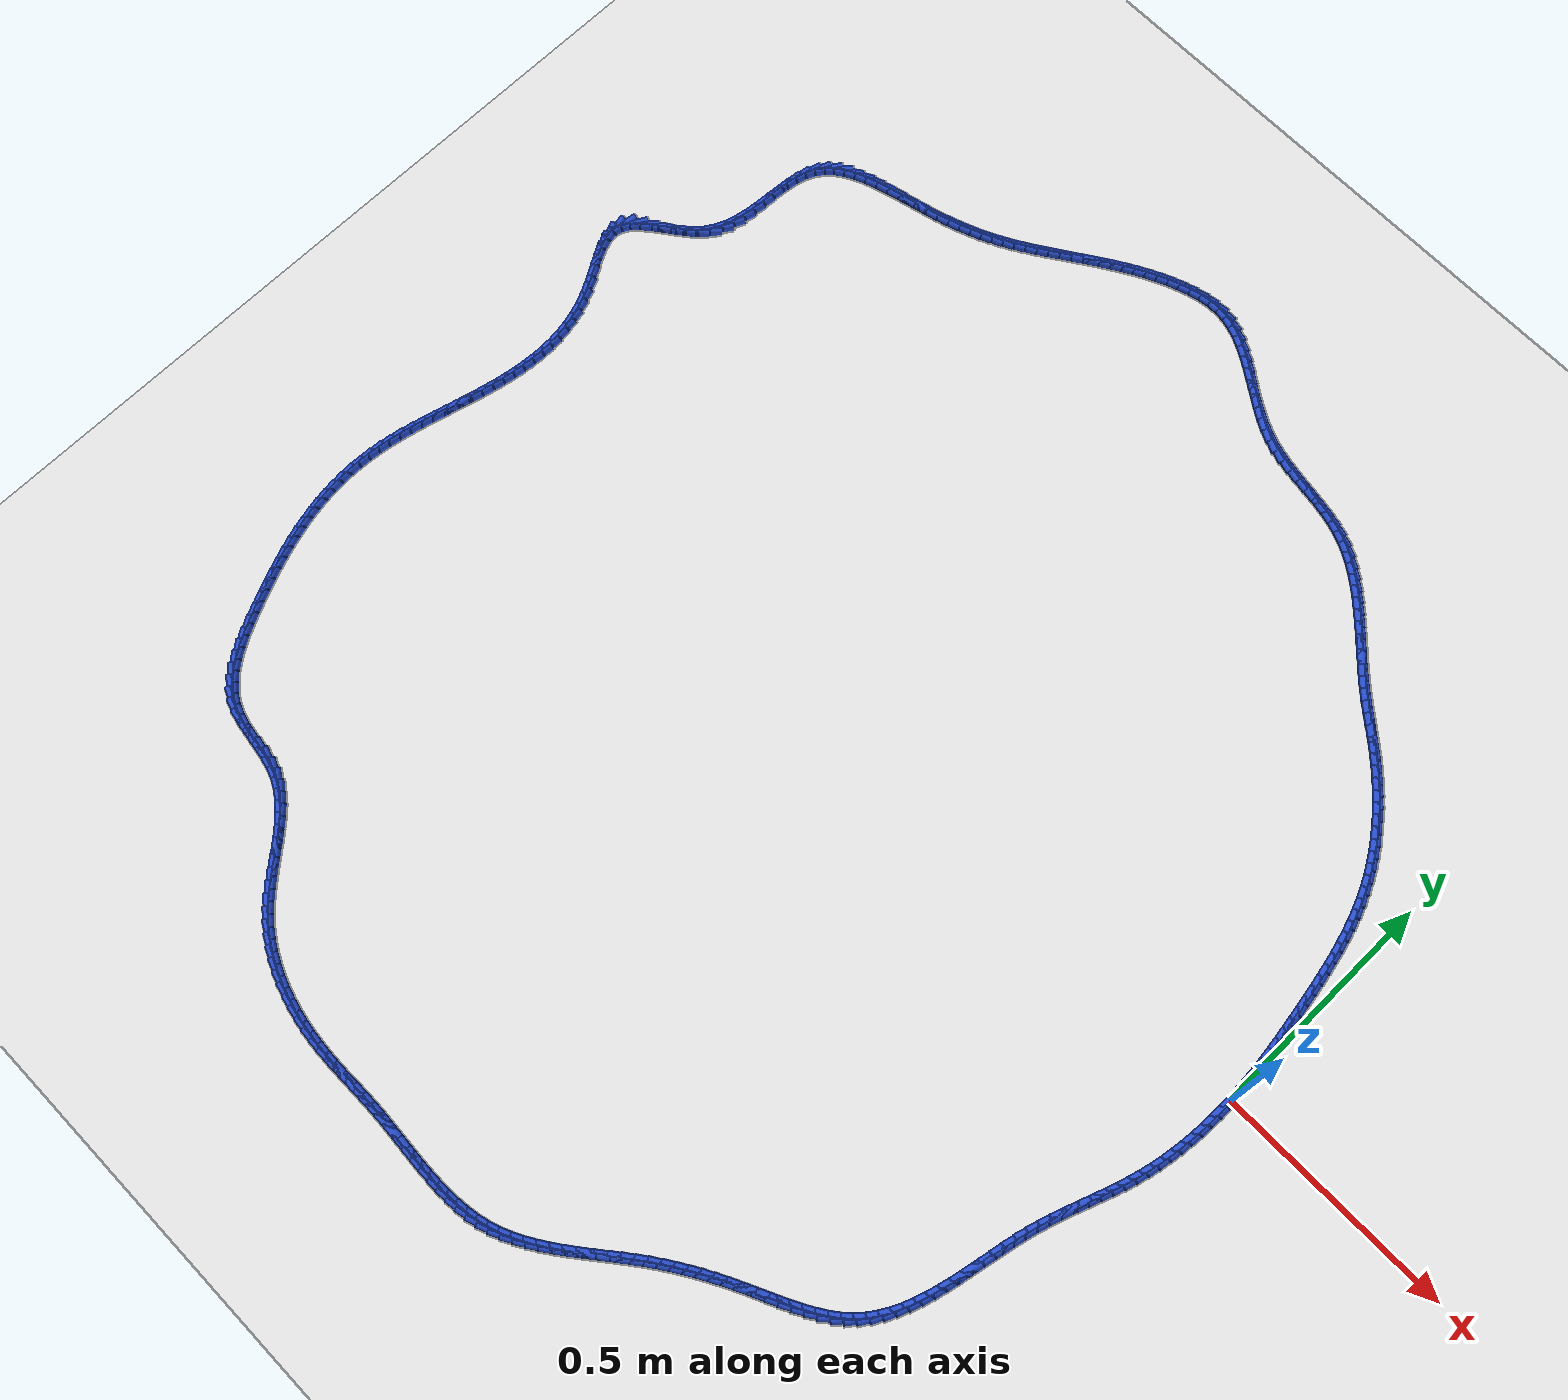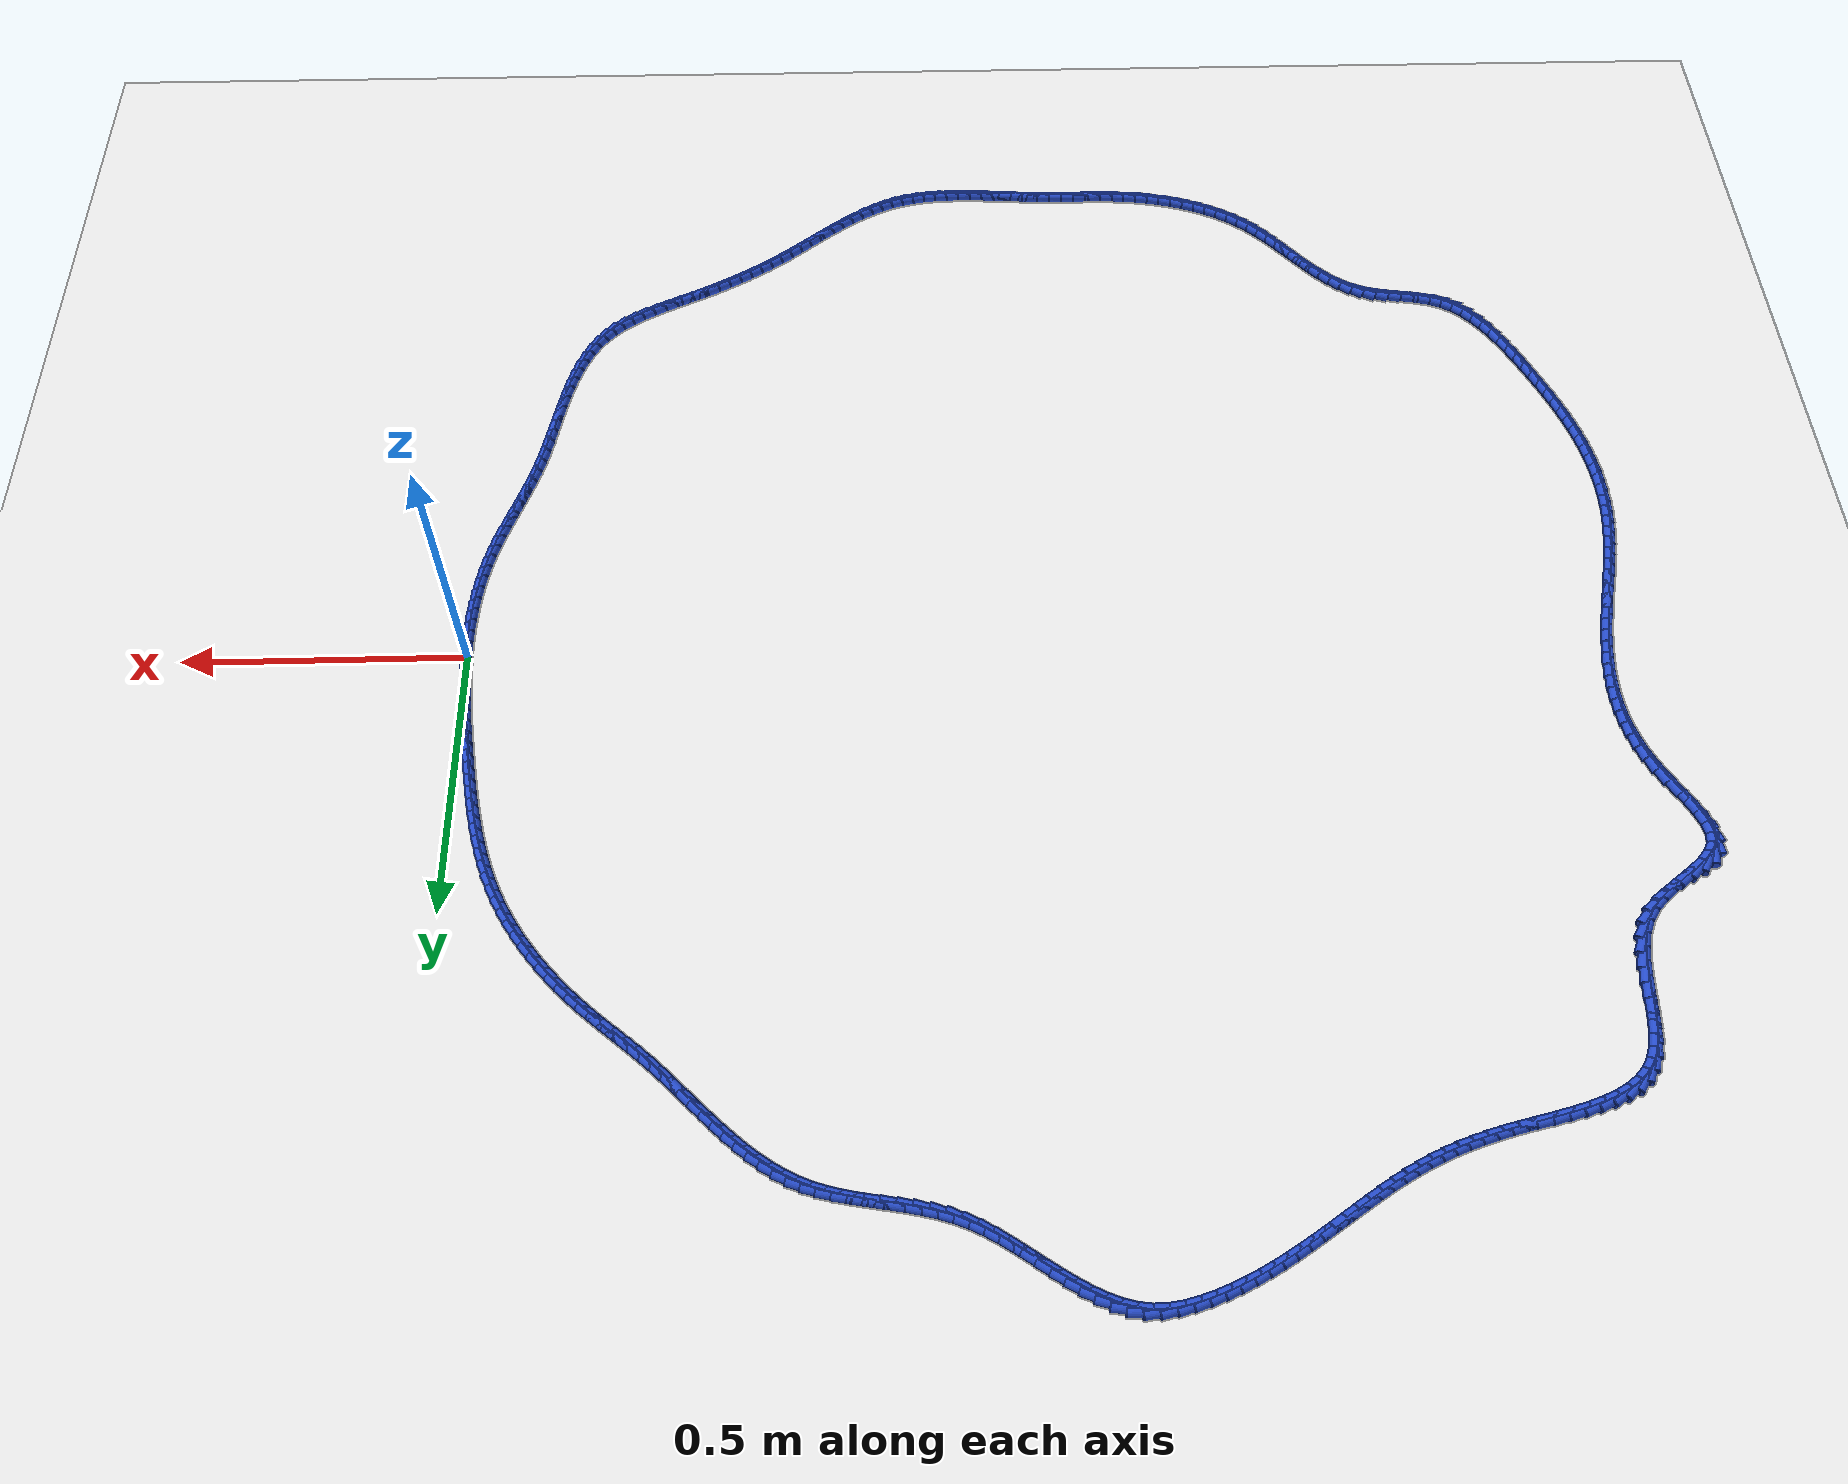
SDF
<sdf version="1.6">
 <world name="default">
  <light name="sun" type="directional">
   <pose>0 0 10 0 -0 0</pose>
   <diffuse>0.8 0.8 0.8 1</diffuse>
   <specular>0.2 0.2 0.2 1</specular>
   <attenuation>
    <range>1000</range>
    <constant>0.9</constant>
    <linear>0.01</linear>
    <quadratic>0.001</quadratic>
   </attenuation>
   <direction>-0.5 0.1 -0.9</direction>
  </light>
  <model name="ground_plane">
   <static>1</static>
   <link name="link">
    <collision name="collision">
     <geometry><plane><normal>0 0 1</normal><size>100 100</size></plane></geometry>
     <surface><friction><ode><mu>100</mu><mu2>50</mu2></ode></friction></surface>
    </collision>
    <visual name="visual">
     <cast_shadows>0</cast_shadows>
     <geometry><plane><normal>0 0 1</normal><size>100 100</size></plane></geometry>
     <material>
      <script><uri>file://media/materials/scripts/gazebo.material</uri><name>Gazebo/WhiteGlow</name></script>
     </material>
    </visual>
   </link>
  </model>
  <gravity>0 0 -9.8</gravity>
  <magnetic_field>6e-06 2.3e-05 -4.2e-05</magnetic_field>
  <atmosphere type="adiabatic"/>
  <physics name="default_physics" default="0" type="ode">
   <max_step_size>0.001</max_step_size>
   <real_time_factor>1</real_time_factor>
   <real_time_update_rate>1000</real_time_update_rate>
  </physics>
  <scene><ambient>0.4 0.4 0.4 1</ambient><background>0.7 0.7 0.7 1</background><shadows>1</shadows></scene>
  <spherical_coordinates>
   <surface_model>EARTH_WGS84</surface_model>
   <latitude_deg>0</latitude_deg>
   <longitude_deg>0</longitude_deg>
   <elevation>0</elevation>
   <heading_deg>0</heading_deg>
  </spherical_coordinates>
  <model name="line">
   <link name="link_0">
    <pose>7.806255641895632e-18 5.551115123125783e-17 0.01 0 1.57 -1.534259723777564</pose>
    <collision name="collision">
     <geometry><cylinder><radius>0.01</radius><length>0.08</length></cylinder></geometry>
    </collision>
    <visual name="visual">
     <material>
      <script><name>Gazebo/Blue</name><uri>file://media/materials/scripts/gazebo.material</uri></script>
     </material>
     <geometry><cylinder><radius>0.01</radius><length>0.08</length></cylinder></geometry>
    </visual>
   </link>
   <link name="link_1">
    <pose>-0.0008810601804037996 0.024103721296122232 0.01 0 1.57 -1.5107745813059357</pose>
    <collision name="collision">
     <geometry><cylinder><radius>0.01</radius><length>0.08</length></cylinder></geometry>
    </collision>
    <visual name="visual">
     <material>
      <script><name>Gazebo/Blue</name><uri>file://media/materials/scripts/gazebo.material</uri></script>
     </material>
     <geometry><cylinder><radius>0.01</radius><length>0.08</length></cylinder></geometry>
    </visual>
   </link>
   <link name="link_2">
    <pose>-0.002324603125221716 0.048125165677702086 0.01 0 1.57 -1.4895934008779321</pose>
    <collision name="collision">
     <geometry><cylinder><radius>0.01</radius><length>0.08</length></cylinder></geometry>
    </collision>
    <visual name="visual">
     <material>
      <script><name>Gazebo/Blue</name><uri>file://media/materials/scripts/gazebo.material</uri></script>
     </material>
     <geometry><cylinder><radius>0.01</radius><length>0.08</length></cylinder></geometry>
    </visual>
   </link>
   <link name="link_3">
    <pose>-0.004274082861389004 0.07207988070871141 0.01 0 1.57 -1.470774897872237</pose>
    <collision name="collision">
     <geometry><cylinder><radius>0.01</radius><length>0.08</length></cylinder></geometry>
    </collision>
    <visual name="visual">
     <material>
      <script><name>Gazebo/Blue</name><uri>file://media/materials/scripts/gazebo.material</uri></script>
     </material>
     <geometry><cylinder><radius>0.01</radius><length>0.08</length></cylinder></geometry>
    </visual>
   </link>
   <link name="link_4">
    <pose>-0.006672953415840927 0.09598341395312208 0.01 0 1.57 -1.454360110415724</pose>
    <collision name="collision">
     <geometry><cylinder><radius>0.01</radius><length>0.08</length></cylinder></geometry>
    </collision>
    <visual name="visual">
     <material>
      <script><name>Gazebo/Blue</name><uri>file://media/materials/scripts/gazebo.material</uri></script>
     </material>
     <geometry><cylinder><radius>0.01</radius><length>0.08</length></cylinder></geometry>
    </visual>
   </link>
   <link name="link_5">
    <pose>-0.009464668815512745 0.11985131297490592 0.01 0 1.57 -1.4403751970826717</pose>
    <collision name="collision">
     <geometry><cylinder><radius>0.01</radius><length>0.08</length></cylinder></geometry>
    </collision>
    <visual name="visual">
     <material>
      <script><name>Gazebo/Blue</name><uri>file://media/materials/scripts/gazebo.material</uri></script>
     </material>
     <geometry><cylinder><radius>0.01</radius><length>0.08</length></cylinder></geometry>
    </visual>
   </link>
   <link name="link_6">
    <pose>-0.012592683087339724 0.14369912533803478 0.01 0 1.57 -1.4288341152202058</pose>
    <collision name="collision">
     <geometry><cylinder><radius>0.01</radius><length>0.08</length></cylinder></geometry>
    </collision>
    <visual name="visual">
     <material>
      <script><name>Gazebo/Blue</name><uri>file://media/materials/scripts/gazebo.material</uri></script>
     </material>
     <geometry><cylinder><radius>0.01</radius><length>0.08</length></cylinder></geometry>
    </visual>
   </link>
   <link name="link_7">
    <pose>-0.01600045025825712 0.1675423986064804 0.01 0 1.57 -1.4197410482318162</pose>
    <collision name="collision">
     <geometry><cylinder><radius>0.01</radius><length>0.08</length></cylinder></geometry>
    </collision>
    <visual name="visual">
     <material>
      <script><name>Gazebo/Blue</name><uri>file://media/materials/scripts/gazebo.material</uri></script>
     </material>
     <geometry><cylinder><radius>0.01</radius><length>0.08</length></cylinder></geometry>
    </visual>
   </link>
   <link name="link_8">
    <pose>-0.0196314243552002 0.19139668034421467 0.01 0 1.57 -1.4130924896593584</pose>
    <collision name="collision">
     <geometry><cylinder><radius>0.01</radius><length>0.08</length></cylinder></geometry>
    </collision>
    <visual name="visual">
     <material>
      <script><name>Gazebo/Blue</name><uri>file://media/materials/scripts/gazebo.material</uri></script>
     </material>
     <geometry><cylinder><radius>0.01</radius><length>0.08</length></cylinder></geometry>
    </visual>
   </link>
   <link name="link_9">
    <pose>-0.023429059454538527 0.21527751809463105 0.01 0 1.57 -1.4078258077938086</pose>
    <collision name="collision">
     <geometry><cylinder><radius>0.01</radius><length>0.08</length></cylinder></geometry>
    </collision>
    <visual name="visual">
     <material>
      <script><name>Gazebo/Blue</name><uri>file://media/materials/scripts/gazebo.material</uri></script>
     </material>
     <geometry><cylinder><radius>0.01</radius><length>0.08</length></cylinder></geometry>
    </visual>
   </link>
   <link name="link_10">
    <pose>-0.02736102292786811 0.23919037988835265 0.01 0 1.57 -1.3998796605443922</pose>
    <collision name="collision">
     <geometry><cylinder><radius>0.01</radius><length>0.08</length></cylinder></geometry>
    </collision>
    <visual name="visual">
     <material>
      <script><name>Gazebo/Blue</name><uri>file://media/materials/scripts/gazebo.material</uri></script>
     </material>
     <geometry><cylinder><radius>0.01</radius><length>0.08</length></cylinder></geometry>
    </visual>
   </link>
   <link name="link_11">
    <pose>-0.03148817368707044 0.26310193997301834 0.01 0 1.57 -1.3882653437921404</pose>
    <collision name="collision">
     <geometry><cylinder><radius>0.01</radius><length>0.08</length></cylinder></geometry>
    </collision>
    <visual name="visual">
     <material>
      <script><name>Gazebo/Blue</name><uri>file://media/materials/scripts/gazebo.material</uri></script>
     </material>
     <geometry><cylinder><radius>0.01</radius><length>0.08</length></cylinder></geometry>
    </visual>
   </link>
   <link name="link_12">
    <pose>-0.03589378747307117 0.2869695409166048 0.01 0 1.57 -1.3729497491673839</pose>
    <collision name="collision">
     <geometry><cylinder><radius>0.01</radius><length>0.08</length></cylinder></geometry>
    </collision>
    <visual name="visual">
     <material>
      <script><name>Gazebo/Blue</name><uri>file://media/materials/scripts/gazebo.material</uri></script>
     </material>
     <geometry><cylinder><radius>0.01</radius><length>0.08</length></cylinder></geometry>
    </visual>
   </link>
   <link name="link_13">
    <pose>-0.04066114002679593 0.3107505252870892 0.01 0 1.57 -1.3538834673669393</pose>
    <collision name="collision">
     <geometry><cylinder><radius>0.01</radius><length>0.08</length></cylinder></geometry>
    </collision>
    <visual name="visual">
     <material>
      <script><name>Gazebo/Blue</name><uri>file://media/materials/scripts/gazebo.material</uri></script>
     </material>
     <geometry><cylinder><radius>0.01</radius><length>0.08</length></cylinder></geometry>
    </visual>
   </link>
   <link name="link_14">
    <pose>-0.04587350708917035 0.3344022356524479 0.01 0 1.57 -1.3310067687901515</pose>
    <collision name="collision">
     <geometry><cylinder><radius>0.01</radius><length>0.08</length></cylinder></geometry>
    </collision>
    <visual name="visual">
     <material>
      <script><name>Gazebo/Blue</name><uri>file://media/materials/scripts/gazebo.material</uri></script>
     </material>
     <geometry><cylinder><radius>0.01</radius><length>0.08</length></cylinder></geometry>
    </visual>
   </link>
   <link name="link_15">
    <pose>-0.05161416440112008 0.35788201458065805 0.01 0 1.57 -1.3042573915515727</pose>
    <collision name="collision">
     <geometry><cylinder><radius>0.01</radius><length>0.08</length></cylinder></geometry>
    </collision>
    <visual name="visual">
     <material>
      <script><name>Gazebo/Blue</name><uri>file://media/materials/scripts/gazebo.material</uri></script>
     </material>
     <geometry><cylinder><radius>0.01</radius><length>0.08</length></cylinder></geometry>
    </visual>
   </link>
   <link name="link_16">
    <pose>-0.05796638770357074 0.3811472046396963 0.01 0 1.57 -1.2735804389887955</pose>
    <collision name="collision">
     <geometry><cylinder><radius>0.01</radius><length>0.08</length></cylinder></geometry>
    </collision>
    <visual name="visual">
     <material>
      <script><name>Gazebo/Blue</name><uri>file://media/materials/scripts/gazebo.material</uri></script>
     </material>
     <geometry><cylinder><radius>0.01</radius><length>0.08</length></cylinder></geometry>
    </visual>
   </link>
   <link name="link_17">
    <pose>-0.06501345273744799 0.4041551483975397 0.01 0 1.57 -1.238940592452902</pose>
    <collision name="collision">
     <geometry><cylinder><radius>0.01</radius><length>0.08</length></cylinder></geometry>
    </collision>
    <visual name="visual">
     <material>
      <script><name>Gazebo/Blue</name><uri>file://media/materials/scripts/gazebo.material</uri></script>
     </material>
     <geometry><cylinder><radius>0.01</radius><length>0.08</length></cylinder></geometry>
    </visual>
   </link>
   <link name="link_18">
    <pose>-0.07283863524367745 0.42686318842216486 0.01 0 1.57 -1.2003366212303013</pose>
    <collision name="collision">
     <geometry><cylinder><radius>0.01</radius><length>0.08</length></cylinder></geometry>
    </collision>
    <visual name="visual">
     <material>
      <script><name>Gazebo/Blue</name><uri>file://media/materials/scripts/gazebo.material</uri></script>
     </material>
     <geometry><cylinder><radius>0.01</radius><length>0.08</length></cylinder></geometry>
    </visual>
   </link>
   <link name="link_19">
    <pose>-0.08152521096318474 0.4492286672815486 0.01 0 1.57 -1.1578177838266042</pose>
    <collision name="collision">
     <geometry><cylinder><radius>0.01</radius><length>0.08</length></cylinder></geometry>
    </collision>
    <visual name="visual">
     <material>
      <script><name>Gazebo/Blue</name><uri>file://media/materials/scripts/gazebo.material</uri></script>
     </material>
     <geometry><cylinder><radius>0.01</radius><length>0.08</length></cylinder></geometry>
    </visual>
   </link>
   <link name="link_20">
    <pose>-0.0911564556368956 0.47120892754366817 0.01 0 1.57 -1.1120649812176504</pose>
    <collision name="collision">
     <geometry><cylinder><radius>0.01</radius><length>0.08</length></cylinder></geometry>
    </collision>
    <visual name="visual">
     <material>
      <script><name>Gazebo/Blue</name><uri>file://media/materials/scripts/gazebo.material</uri></script>
     </material>
     <geometry><cylinder><radius>0.01</radius><length>0.08</length></cylinder></geometry>
    </visual>
   </link>
   <link name="link_21">
    <pose>-0.10180172579984494 0.4927637432552224 0.01 0 1.57 -1.066969201448135</pose>
    <collision name="collision">
     <geometry><cylinder><radius>0.01</radius><length>0.08</length></cylinder></geometry>
    </collision>
    <visual name="visual">
     <material>
      <script><name>Gazebo/Blue</name><uri>file://media/materials/scripts/gazebo.material</uri></script>
     </material>
     <geometry><cylinder><radius>0.01</radius><length>0.08</length></cylinder></geometry>
    </visual>
   </link>
   <link name="link_22">
    <pose>-0.11343680794213319 0.5138692337612801 0.01 0 1.57 -1.0240342662497106</pose>
    <collision name="collision">
     <geometry><cylinder><radius>0.01</radius><length>0.08</length></cylinder></geometry>
    </collision>
    <visual name="visual">
     <material>
      <script><name>Gazebo/Blue</name><uri>file://media/materials/scripts/gazebo.material</uri></script>
     </material>
     <geometry><cylinder><radius>0.01</radius><length>0.08</length></cylinder></geometry>
    </visual>
   </link>
   <link name="link_23">
    <pose>-0.1259989321141269 0.5345082536447942 0.01 0 1.57 -0.9831604393416739</pose>
    <collision name="collision">
     <geometry><cylinder><radius>0.01</radius><length>0.08</length></cylinder></geometry>
    </collision>
    <visual name="visual">
     <material>
      <script><name>Gazebo/Blue</name><uri>file://media/materials/scripts/gazebo.material</uri></script>
     </material>
     <geometry><cylinder><radius>0.01</radius><length>0.08</length></cylinder></geometry>
    </visual>
   </link>
   <link name="link_24">
    <pose>-0.13942520825737797 0.5546636784699449 0.01 0 1.57 -0.9442263243144104</pose>
    <collision name="collision">
     <geometry><cylinder><radius>0.01</radius><length>0.08</length></cylinder></geometry>
    </collision>
    <visual name="visual">
     <material>
      <script><name>Gazebo/Blue</name><uri>file://media/materials/scripts/gazebo.material</uri></script>
     </material>
     <geometry><cylinder><radius>0.01</radius><length>0.08</length></cylinder></geometry>
    </visual>
   </link>
   <link name="link_25">
    <pose>-0.15365274631343825 0.5743183838009129 0.01 0 1.57 -0.9070990932670701</pose>
    <collision name="collision">
     <geometry><cylinder><radius>0.01</radius><length>0.08</length></cylinder></geometry>
    </collision>
    <visual name="visual">
     <material>
      <script><name>Gazebo/Blue</name><uri>file://media/materials/scripts/gazebo.material</uri></script>
     </material>
     <geometry><cylinder><radius>0.01</radius><length>0.08</length></cylinder></geometry>
    </visual>
   </link>
   <link name="link_26">
    <pose>-0.16861865622385946 0.5934552452018785 0.01 0 1.57 -0.8716386688690076</pose>
    <collision name="collision">
     <geometry><cylinder><radius>0.01</radius><length>0.08</length></cylinder></geometry>
    </collision>
    <visual name="visual">
     <material>
      <script><name>Gazebo/Blue</name><uri>file://media/materials/scripts/gazebo.material</uri></script>
     </material>
     <geometry><cylinder><radius>0.01</radius><length>0.08</length></cylinder></geometry>
    </visual>
   </link>
   <link name="link_27">
    <pose>-0.18426004793019363 0.6120571382370221 0.01 0 1.57 -0.8377008184548389</pose>
    <collision name="collision">
     <geometry><cylinder><radius>0.01</radius><length>0.08</length></cylinder></geometry>
    </collision>
    <visual name="visual">
     <material>
      <script><name>Gazebo/Blue</name><uri>file://media/materials/scripts/gazebo.material</uri></script>
     </material>
     <geometry><cylinder><radius>0.01</radius><length>0.08</length></cylinder></geometry>
    </visual>
   </link>
   <link name="link_28">
    <pose>-0.2005140313739927 0.6301069384705245 0.01 0 1.57 -0.8051392859692186</pose>
    <collision name="collision">
     <geometry><cylinder><radius>0.01</radius><length>0.08</length></cylinder></geometry>
    </collision>
    <visual name="visual">
     <material>
      <script><name>Gazebo/Blue</name><uri>file://media/materials/scripts/gazebo.material</uri></script>
     </material>
     <geometry><cylinder><radius>0.01</radius><length>0.08</length></cylinder></geometry>
    </visual>
   </link>
   <link name="link_29">
    <pose>-0.21731771649680842 0.647587521466566 0.01 0 1.57 -0.7738070939068152</pose>
    <collision name="collision">
     <geometry><cylinder><radius>0.01</radius><length>0.08</length></cylinder></geometry>
    </collision>
    <visual name="visual">
     <material>
      <script><name>Gazebo/Blue</name><uri>file://media/materials/scripts/gazebo.material</uri></script>
     </material>
     <geometry><cylinder><radius>0.01</radius><length>0.08</length></cylinder></geometry>
    </visual>
   </link>
   <link name="link_30">
    <pose>-0.23460821324019268 0.6644817627893269 0.01 0 1.57 -0.7436995711177722</pose>
    <collision name="collision">
     <geometry><cylinder><radius>0.01</radius><length>0.08</length></cylinder></geometry>
    </collision>
    <visual name="visual">
     <material>
      <script><name>Gazebo/Blue</name><uri>file://media/materials/scripts/gazebo.material</uri></script>
     </material>
     <geometry><cylinder><radius>0.01</radius><length>0.08</length></cylinder></geometry>
    </visual>
   </link>
   <link name="link_31">
    <pose>-0.252321800210542 0.6807764309087913 0.01 0 1.57 -0.7185550530422332</pose>
    <collision name="collision">
     <geometry><cylinder><radius>0.01</radius><length>0.08</length></cylinder></geometry>
    </collision>
    <visual name="visual">
     <material>
      <script><name>Gazebo/Blue</name><uri>file://media/materials/scripts/gazebo.material</uri></script>
     </material>
     <geometry><cylinder><radius>0.01</radius><length>0.08</length></cylinder></geometry>
    </visual>
   </link>
   <link name="link_32">
    <pose>-0.27037258642767936 0.6965621081559228 0.01 0 1.57 -0.702691066058689</pose>
    <collision name="collision">
     <geometry><cylinder><radius>0.01</radius><length>0.08</length></cylinder></geometry>
    </collision>
    <visual name="visual">
     <material>
      <script><name>Gazebo/Blue</name><uri>file://media/materials/scripts/gazebo.material</uri></script>
     </material>
     <geometry><cylinder><radius>0.01</radius><length>0.08</length></cylinder></geometry>
    </visual>
   </link>
   <link name="link_33">
    <pose>-0.2886506723006257 0.712041802349447 0.01 0 1.57 -0.6964608282099027</pose>
    <collision name="collision">
     <geometry><cylinder><radius>0.01</radius><length>0.08</length></cylinder></geometry>
    </collision>
    <visual name="visual">
     <material>
      <script><name>Gazebo/Blue</name><uri>file://media/materials/scripts/gazebo.material</uri></script>
     </material>
     <geometry><cylinder><radius>0.01</radius><length>0.08</length></cylinder></geometry>
    </visual>
   </link>
   <link name="link_34">
    <pose>-0.30704495836601525 0.7274241399688044 0.01 0 1.57 -0.6998733784807241</pose>
    <collision name="collision">
     <geometry><cylinder><radius>0.01</radius><length>0.08</length></cylinder></geometry>
    </collision>
    <visual name="visual">
     <material>
      <script><name>Gazebo/Blue</name><uri>file://media/materials/scripts/gazebo.material</uri></script>
     </material>
     <geometry><cylinder><radius>0.01</radius><length>0.08</length></cylinder></geometry>
    </visual>
   </link>
   <link name="link_35">
    <pose>-0.3254443451604827 0.7429177474934352 0.01 0 1.57 -0.7128167071255693</pose>
    <collision name="collision">
     <geometry><cylinder><radius>0.01</radius><length>0.08</length></cylinder></geometry>
    </collision>
    <visual name="visual">
     <material>
      <script><name>Gazebo/Blue</name><uri>file://media/materials/scripts/gazebo.material</uri></script>
     </material>
     <geometry><cylinder><radius>0.01</radius><length>0.08</length></cylinder></geometry>
    </visual>
   </link>
   <link name="link_36">
    <pose>-0.3437377332206625 0.75873125140278 0.01 0 1.57 -0.7349488194673364</pose>
    <collision name="collision">
     <geometry><cylinder><radius>0.01</radius><length>0.08</length></cylinder></geometry>
    </collision>
    <visual name="visual">
     <material>
      <script><name>Gazebo/Blue</name><uri>file://media/materials/scripts/gazebo.material</uri></script>
     </material>
     <geometry><cylinder><radius>0.01</radius><length>0.08</length></cylinder></geometry>
    </visual>
   </link>
   <link name="link_37">
    <pose>-0.3618151849092859 0.7750709079997502 0.01 0 1.57 -0.7595095492451638</pose>
    <collision name="collision">
     <geometry><cylinder><radius>0.01</radius><length>0.08</length></cylinder></geometry>
    </collision>
    <visual name="visual">
     <material>
      <script><name>Gazebo/Blue</name><uri>file://media/materials/scripts/gazebo.material</uri></script>
     </material>
     <geometry><cylinder><radius>0.01</radius><length>0.08</length></cylinder></geometry>
    </visual>
   </link>
   <link name="link_38">
    <pose>-0.37963922004346307 0.7919951571815517 0.01 0 1.57 -0.7764745601534427</pose>
    <collision name="collision">
     <geometry><cylinder><radius>0.01</radius><length>0.08</length></cylinder></geometry>
    </collision>
    <visual name="visual">
     <material>
      <script><name>Gazebo/Blue</name><uri>file://media/materials/scripts/gazebo.material</uri></script>
     </material>
     <geometry><cylinder><radius>0.01</radius><length>0.08</length></cylinder></geometry>
    </visual>
   </link>
   <link name="link_39">
    <pose>-0.39728627668958955 0.8093300405877113 0.01 0 1.57 -0.7852464354962679</pose>
    <collision name="collision">
     <geometry><cylinder><radius>0.01</radius><length>0.08</length></cylinder></geometry>
    </collision>
    <visual name="visual">
     <material>
      <script><name>Gazebo/Blue</name><uri>file://media/materials/scripts/gazebo.material</uri></script>
     </material>
     <geometry><cylinder><radius>0.01</radius><length>0.08</length></cylinder></geometry>
    </visual>
   </link>
   <link name="link_40">
    <pose>-0.41484278285485815 0.8268812199375005 0.01 0 1.57 -0.7859889964515014</pose>
    <collision name="collision">
     <geometry><cylinder><radius>0.01</radius><length>0.08</length></cylinder></geometry>
    </collision>
    <visual name="visual">
     <material>
      <script><name>Gazebo/Blue</name><uri>file://media/materials/scripts/gazebo.material</uri></script>
     </material>
     <geometry><cylinder><radius>0.01</radius><length>0.08</length></cylinder></geometry>
    </visual>
   </link>
   <link name="link_41">
    <pose>-0.4323951665464626 0.8444543569501928 0.01 0 1.57 -0.7787212295163041</pose>
    <collision name="collision">
     <geometry><cylinder><radius>0.01</radius><length>0.08</length></cylinder></geometry>
    </collision>
    <visual name="visual">
     <material>
      <script><name>Gazebo/Blue</name><uri>file://media/materials/scripts/gazebo.material</uri></script>
     </material>
     <geometry><cylinder><radius>0.01</radius><length>0.08</length></cylinder></geometry>
    </visual>
   </link>
   <link name="link_42">
    <pose>-0.45002985577159643 0.8618551133450605 0.01 0 1.57 -0.7633167541371441</pose>
    <collision name="collision">
     <geometry><cylinder><radius>0.01</radius><length>0.08</length></cylinder></geometry>
    </collision>
    <visual name="visual">
     <material>
      <script><name>Gazebo/Blue</name><uri>file://media/materials/scripts/gazebo.material</uri></script>
     </material>
     <geometry><cylinder><radius>0.01</radius><length>0.08</length></cylinder></geometry>
    </visual>
   </link>
   <link name="link_43">
    <pose>-0.4678332785374528 0.8788891508413755 0.01 0 1.57 -0.73951286834374</pose>
    <collision name="collision">
     <geometry><cylinder><radius>0.01</radius><length>0.08</length></cylinder></geometry>
    </collision>
    <visual name="visual">
     <material>
      <script><name>Gazebo/Blue</name><uri>file://media/materials/scripts/gazebo.material</uri></script>
     </material>
     <geometry><cylinder><radius>0.01</radius><length>0.08</length></cylinder></geometry>
    </visual>
   </link>
   <link name="link_44">
    <pose>-0.4858918628512257 0.8953621311584112 0.01 0 1.57 -0.7069322449732386</pose>
    <collision name="collision">
     <geometry><cylinder><radius>0.01</radius><length>0.08</length></cylinder></geometry>
    </collision>
    <visual name="visual">
     <material>
      <script><name>Gazebo/Blue</name><uri>file://media/materials/scripts/gazebo.material</uri></script>
     </material>
     <geometry><cylinder><radius>0.01</radius><length>0.08</length></cylinder></geometry>
    </visual>
   </link>
   <link name="link_45">
    <pose>-0.5042920367201082 0.9110797160154395 0.01 0 1.57 -0.6651238023309737</pose>
    <collision name="collision">
     <geometry><cylinder><radius>0.01</radius><length>0.08</length></cylinder></geometry>
    </collision>
    <visual name="visual">
     <material>
      <script><name>Gazebo/Blue</name><uri>file://media/materials/scripts/gazebo.material</uri></script>
     </material>
     <geometry><cylinder><radius>0.01</radius><length>0.08</length></cylinder></geometry>
    </visual>
   </link>
   <link name="link_46">
    <pose>-0.5231202281512937 0.9258475671317327 0.01 0 1.57 -0.6136323024679909</pose>
    <collision name="collision">
     <geometry><cylinder><radius>0.01</radius><length>0.08</length></cylinder></geometry>
    </collision>
    <visual name="visual">
     <material>
      <script><name>Gazebo/Blue</name><uri>file://media/materials/scripts/gazebo.material</uri></script>
     </material>
     <geometry><cylinder><radius>0.01</radius><length>0.08</length></cylinder></geometry>
    </visual>
   </link>
   <link name="link_47">
    <pose>-0.542462865151976 0.939471346226564 0.01 0 1.57 -0.5521072558134386</pose>
    <collision name="collision">
     <geometry><cylinder><radius>0.01</radius><length>0.08</length></cylinder></geometry>
    </collision>
    <visual name="visual">
     <material>
      <script><name>Gazebo/Blue</name><uri>file://media/materials/scripts/gazebo.material</uri></script>
     </material>
     <geometry><cylinder><radius>0.01</radius><length>0.08</length></cylinder></geometry>
    </visual>
   </link>
   <link name="link_48">
    <pose>-0.5624063757293483 0.9517567150192054 0.01 0 1.57 -0.48045734838819515</pose>
    <collision name="collision">
     <geometry><cylinder><radius>0.01</radius><length>0.08</length></cylinder></geometry>
    </collision>
    <visual name="visual">
     <material>
      <script><name>Gazebo/Blue</name><uri>file://media/materials/scripts/gazebo.material</uri></script>
     </material>
     <geometry><cylinder><radius>0.01</radius><length>0.08</length></cylinder></geometry>
    </visual>
   </link>
   <link name="link_49">
    <pose>-0.5830371878906041 0.9625093352289295 0.01 0 1.57 -0.3991096197134732</pose>
    <collision name="collision">
     <geometry><cylinder><radius>0.01</radius><length>0.08</length></cylinder></geometry>
    </collision>
    <visual name="visual">
     <material>
      <script><name>Gazebo/Blue</name><uri>file://media/materials/scripts/gazebo.material</uri></script>
     </material>
     <geometry><cylinder><radius>0.01</radius><length>0.08</length></cylinder></geometry>
    </visual>
   </link>
   <link name="link_50">
    <pose>-0.6044411503199689 0.9715363295434094 0.01 0 1.57 -0.3175064259588838</pose>
    <collision name="collision">
     <geometry><cylinder><radius>0.01</radius><length>0.08</length></cylinder></geometry>
    </collision>
    <visual name="visual">
     <material>
      <script><name>Gazebo/Blue</name><uri>file://media/materials/scripts/gazebo.material</uri></script>
     </material>
     <geometry><cylinder><radius>0.01</radius><length>0.08</length></cylinder></geometry>
    </visual>
   </link>
   <link name="link_51">
    <pose>-0.6266312613865792 0.9788285385662269 0.01 0 1.57 -0.25309000842806595</pose>
    <collision name="collision">
     <geometry><cylinder><radius>0.01</radius><length>0.08</length></cylinder></geometry>
    </collision>
    <visual name="visual">
     <material>
      <script><name>Gazebo/Blue</name><uri>file://media/materials/scripts/gazebo.material</uri></script>
     </material>
     <geometry><cylinder><radius>0.01</radius><length>0.08</length></cylinder></geometry>
    </visual>
   </link>
   <link name="link_52">
    <pose>-0.6494775283159376 0.9847374058011713 0.01 0 1.57 -0.20757520173808963</pose>
    <collision name="collision">
     <geometry><cylinder><radius>0.01</radius><length>0.08</length></cylinder></geometry>
    </collision>
    <visual name="visual">
     <material>
      <script><name>Gazebo/Blue</name><uri>file://media/materials/scripts/gazebo.material</uri></script>
     </material>
     <geometry><cylinder><radius>0.01</radius><length>0.08</length></cylinder></geometry>
    </visual>
   </link>
   <link name="link_53">
    <pose>-0.6728333175558965 0.9896563403768219 0.01 0 1.57 -0.18025849099294847</pose>
    <collision name="collision">
     <geometry><cylinder><radius>0.01</radius><length>0.08</length></cylinder></geometry>
    </collision>
    <visual name="visual">
     <material>
      <script><name>Gazebo/Blue</name><uri>file://media/materials/scripts/gazebo.material</uri></script>
     </material>
     <geometry><cylinder><radius>0.01</radius><length>0.08</length></cylinder></geometry>
    </visual>
   </link>
   <link name="link_54">
    <pose>-0.6965519955543079 0.9939787514217587 0.01 0 1.57 -0.170434301298606</pose>
    <collision name="collision">
     <geometry><cylinder><radius>0.01</radius><length>0.08</length></cylinder></geometry>
    </collision>
    <visual name="visual">
     <material>
      <script><name>Gazebo/Blue</name><uri>file://media/materials/scripts/gazebo.material</uri></script>
     </material>
     <geometry><cylinder><radius>0.01</radius><length>0.08</length></cylinder></geometry>
    </visual>
   </link>
   <link name="link_55">
    <pose>-0.720486928759025 0.9980980480645618 0.01 0 1.57 -0.1776398156680651</pose>
    <collision name="collision">
     <geometry><cylinder><radius>0.01</radius><length>0.08</length></cylinder></geometry>
    </collision>
    <visual name="visual">
     <material>
      <script><name>Gazebo/Blue</name><uri>file://media/materials/scripts/gazebo.material</uri></script>
     </material>
     <geometry><cylinder><radius>0.01</radius><length>0.08</length></cylinder></geometry>
    </visual>
   </link>
   <link name="link_56">
    <pose>-0.7444914836179 1.0024076394338106 0.01 0 1.57 -0.2017232353086843</pose>
    <collision name="collision">
     <geometry><cylinder><radius>0.01</radius><length>0.08</length></cylinder></geometry>
    </collision>
    <visual name="visual">
     <material>
      <script><name>Gazebo/Blue</name><uri>file://media/materials/scripts/gazebo.material</uri></script>
     </material>
     <geometry><cylinder><radius>0.01</radius><length>0.08</length></cylinder></geometry>
    </visual>
   </link>
   <link name="link_57">
    <pose>-0.768419026578785 1.0073009346580846 0.01 0 1.57 -0.2427711633547543</pose>
    <collision name="collision">
     <geometry><cylinder><radius>0.01</radius><length>0.08</length></cylinder></geometry>
    </collision>
    <visual name="visual">
     <material>
      <script><name>Gazebo/Blue</name><uri>file://media/materials/scripts/gazebo.material</uri></script>
     </material>
     <geometry><cylinder><radius>0.01</radius><length>0.08</length></cylinder></geometry>
    </visual>
   </link>
   <link name="link_58">
    <pose>-0.7921229240895328 1.013171342865964 0.01 0 1.57 -0.30089922278817965</pose>
    <collision name="collision">
     <geometry><cylinder><radius>0.01</radius><length>0.08</length></cylinder></geometry>
    </collision>
    <visual name="visual">
     <material>
      <script><name>Gazebo/Blue</name><uri>file://media/materials/scripts/gazebo.material</uri></script>
     </material>
     <geometry><cylinder><radius>0.01</radius><length>0.08</length></cylinder></geometry>
    </visual>
   </link>
   <link name="link_59">
    <pose>-0.8154565425979957 1.0204122731860286 0.01 0 1.57 -0.3758530031502557</pose>
    <collision name="collision">
     <geometry><cylinder><radius>0.01</radius><length>0.08</length></cylinder></geometry>
    </collision>
    <visual name="visual">
     <material>
      <script><name>Gazebo/Blue</name><uri>file://media/materials/scripts/gazebo.material</uri></script>
     </material>
     <geometry><cylinder><radius>0.01</radius><length>0.08</length></cylinder></geometry>
    </visual>
   </link>
   <link name="link_60">
    <pose>-0.8382735480699083 1.029416139086231 0.01 0 1.57 -0.45685468386679484</pose>
    <collision name="collision">
     <geometry><cylinder><radius>0.01</radius><length>0.08</length></cylinder></geometry>
    </collision>
    <visual name="visual">
     <material>
      <script><name>Gazebo/Blue</name><uri>file://media/materials/scripts/gazebo.material</uri></script>
     </material>
     <geometry><cylinder><radius>0.01</radius><length>0.08</length></cylinder></geometry>
    </visual>
   </link>
   <link name="link_61">
    <pose>-0.860498278173993 1.040340426384787 0.01 0 1.57 -0.5210684827153949</pose>
    <collision name="collision">
     <geometry><cylinder><radius>0.01</radius><length>0.08</length></cylinder></geometry>
    </collision>
    <visual name="visual">
     <material>
      <script><name>Gazebo/Blue</name><uri>file://media/materials/scripts/gazebo.material</uri></script>
     </material>
     <geometry><cylinder><radius>0.01</radius><length>0.08</length></cylinder></geometry>
    </visual>
   </link>
   <link name="link_62">
    <pose>-0.8822164262227498 1.0528062407001735 0.01 0 1.57 -0.566290844780955</pose>
    <collision name="collision">
     <geometry><cylinder><radius>0.01</radius><length>0.08</length></cylinder></geometry>
    </collision>
    <visual name="visual">
     <material>
      <script><name>Gazebo/Blue</name><uri>file://media/materials/scripts/gazebo.material</uri></script>
     </material>
     <geometry><cylinder><radius>0.01</radius><length>0.08</length></cylinder></geometry>
    </visual>
   </link>
   <link name="link_63">
    <pose>-0.9035360996010947 1.0663601785456502 0.01 0 1.57 -0.5935495885012775</pose>
    <collision name="collision">
     <geometry><cylinder><radius>0.01</radius><length>0.08</length></cylinder></geometry>
    </collision>
    <visual name="visual">
     <material>
      <script><name>Gazebo/Blue</name><uri>file://media/materials/scripts/gazebo.material</uri></script>
     </material>
     <geometry><cylinder><radius>0.01</radius><length>0.08</length></cylinder></geometry>
    </visual>
   </link>
   <link name="link_64">
    <pose>-0.9245654056939439 1.0805488364344775 0.01 0 1.57 -0.6035120312592145</pose>
    <collision name="collision">
     <geometry><cylinder><radius>0.01</radius><length>0.08</length></cylinder></geometry>
    </collision>
    <visual name="visual">
     <material>
      <script><name>Gazebo/Blue</name><uri>file://media/materials/scripts/gazebo.material</uri></script>
     </material>
     <geometry><cylinder><radius>0.01</radius><length>0.08</length></cylinder></geometry>
    </visual>
   </link>
   <link name="link_65">
    <pose>-0.9454124518862134 1.0949188108799155 0.01 0 1.57 -0.5962649100023555</pose>
    <collision name="collision">
     <geometry><cylinder><radius>0.01</radius><length>0.08</length></cylinder></geometry>
    </collision>
    <visual name="visual">
     <material>
      <script><name>Gazebo/Blue</name><uri>file://media/materials/scripts/gazebo.material</uri></script>
     </material>
     <geometry><cylinder><radius>0.01</radius><length>0.08</length></cylinder></geometry>
    </visual>
   </link>
   <link name="link_66">
    <pose>-0.9661853455628191 1.1090166983952239 0.01 0 1.57 -0.5712206868498659</pose>
    <collision name="collision">
     <geometry><cylinder><radius>0.01</radius><length>0.08</length></cylinder></geometry>
    </collision>
    <visual name="visual">
     <material>
      <script><name>Gazebo/Blue</name><uri>file://media/materials/scripts/gazebo.material</uri></script>
     </material>
     <geometry><cylinder><radius>0.01</radius><length>0.08</length></cylinder></geometry>
    </visual>
   </link>
   <link name="link_67">
    <pose>-0.9869921941086768 1.1223890954936628 0.01 0 1.57 -0.5271231632081871</pose>
    <collision name="collision">
     <geometry><cylinder><radius>0.01</radius><length>0.08</length></cylinder></geometry>
    </collision>
    <visual name="visual">
     <material>
      <script><name>Gazebo/Blue</name><uri>file://media/materials/scripts/gazebo.material</uri></script>
     </material>
     <geometry><cylinder><radius>0.01</radius><length>0.08</length></cylinder></geometry>
    </visual>
   </link>
   <link name="link_68">
    <pose>-1.0079411049087028 1.1345825986884923 0.01 0 1.57 -0.46219991841477687</pose>
    <collision name="collision">
     <geometry><cylinder><radius>0.01</radius><length>0.08</length></cylinder></geometry>
    </collision>
    <visual name="visual">
     <material>
      <script><name>Gazebo/Blue</name><uri>file://media/materials/scripts/gazebo.material</uri></script>
     </material>
     <geometry><cylinder><radius>0.01</radius><length>0.08</length></cylinder></geometry>
    </visual>
   </link>
   <link name="link_69">
    <pose>-1.0291401853478133 1.1451438044929727 0.01 0 1.57 -0.37459652682225225</pose>
    <collision name="collision">
     <geometry><cylinder><radius>0.01</radius><length>0.08</length></cylinder></geometry>
    </collision>
    <visual name="visual">
     <material>
      <script><name>Gazebo/Blue</name><uri>file://media/materials/scripts/gazebo.material</uri></script>
     </material>
     <geometry><cylinder><radius>0.01</radius><length>0.08</length></cylinder></geometry>
    </visual>
   </link>
   <link name="link_70">
    <pose>-1.0506975428109242 1.153619309420364 0.01 0 1.57 -0.26328816986447695</pose>
    <collision name="collision">
     <geometry><cylinder><radius>0.01</radius><length>0.08</length></cylinder></geometry>
    </collision>
    <visual name="visual">
     <material>
      <script><name>Gazebo/Blue</name><uri>file://media/materials/scripts/gazebo.material</uri></script>
     </material>
     <geometry><cylinder><radius>0.01</radius><length>0.08</length></cylinder></geometry>
    </visual>
   </link>
   <link name="link_71">
    <pose>-1.0727212846829515 1.159555709983926 0.01 0 1.57 -0.12954141335783242</pose>
    <collision name="collision">
     <geometry><cylinder><radius>0.01</radius><length>0.08</length></cylinder></geometry>
    </collision>
    <visual name="visual">
     <material>
      <script><name>Gazebo/Blue</name><uri>file://media/materials/scripts/gazebo.material</uri></script>
     </material>
     <geometry><cylinder><radius>0.01</radius><length>0.08</length></cylinder></geometry>
    </visual>
   </link>
   <link name="link_72">
    <pose>-1.095319518348811 1.162499602696919 0.01 0 1.57 0.01829741381164803</pose>
    <collision name="collision">
     <geometry><cylinder><radius>0.01</radius><length>0.08</length></cylinder></geometry>
    </collision>
    <visual name="visual">
     <material>
      <script><name>Gazebo/Blue</name><uri>file://media/materials/scripts/gazebo.material</uri></script>
     </material>
     <geometry><cylinder><radius>0.01</radius><length>0.08</length></cylinder></geometry>
    </visual>
   </link>
   <link name="link_73">
    <pose>-1.1185687767045964 1.1620741539154846 0.01 0 1.57 0.14616884977913375</pose>
    <collision name="collision">
     <geometry><cylinder><radius>0.01</radius><length>0.08</length></cylinder></geometry>
    </collision>
    <visual name="visual">
     <material>
      <script><name>Gazebo/Blue</name><uri>file://media/materials/scripts/gazebo.material</uri></script>
     </material>
     <geometry><cylinder><radius>0.01</radius><length>0.08</length></cylinder></geometry>
    </visual>
   </link>
   <link name="link_74">
    <pose>-1.142263840178189 1.1585857949677996 0.01 0 1.57 0.24255863920379583</pose>
    <collision name="collision">
     <geometry><cylinder><radius>0.01</radius><length>0.08</length></cylinder></geometry>
    </collision>
    <visual name="visual">
     <material>
      <script><name>Gazebo/Blue</name><uri>file://media/materials/scripts/gazebo.material</uri></script>
     </material>
     <geometry><cylinder><radius>0.01</radius><length>0.08</length></cylinder></geometry>
    </visual>
   </link>
   <link name="link_75">
    <pose>-1.1660514224911565 1.1527000269520096 0.01 0 1.57 0.31302887787069433</pose>
    <collision name="collision">
     <geometry><cylinder><radius>0.01</radius><length>0.08</length></cylinder></geometry>
    </collision>
    <visual name="visual">
     <material>
      <script><name>Gazebo/Blue</name><uri>file://media/materials/scripts/gazebo.material</uri></script>
     </material>
     <geometry><cylinder><radius>0.01</radius><length>0.08</length></cylinder></geometry>
    </visual>
   </link>
   <link name="link_76">
    <pose>-1.1895769446468005 1.1450855111065605 0.01 0 1.57 0.3650162050414237</pose>
    <collision name="collision">
     <geometry><cylinder><radius>0.01</radius><length>0.08</length></cylinder></geometry>
    </collision>
    <visual name="visual">
     <material>
      <script><name>Gazebo/Blue</name><uri>file://media/materials/scripts/gazebo.material</uri></script>
     </material>
     <geometry><cylinder><radius>0.01</radius><length>0.08</length></cylinder></geometry>
    </visual>
   </link>
   <link name="link_77">
    <pose>-1.212569343120712 1.1362991814722798 0.01 0 1.57 0.41009348464583384</pose>
    <collision name="collision">
     <geometry><cylinder><radius>0.01</radius><length>0.08</length></cylinder></geometry>
    </collision>
    <visual name="visual">
     <material>
      <script><name>Gazebo/Blue</name><uri>file://media/materials/scripts/gazebo.material</uri></script>
     </material>
     <geometry><cylinder><radius>0.01</radius><length>0.08</length></cylinder></geometry>
    </visual>
   </link>
   <link name="link_78">
    <pose>-1.2350287941676457 1.1265351068677885 0.01 0 1.57 0.45010851367796106</pose>
    <collision name="collision">
     <geometry><cylinder><radius>0.01</radius><length>0.08</length></cylinder></geometry>
    </collision>
    <visual name="visual">
     <material>
      <script><name>Gazebo/Blue</name><uri>file://media/materials/scripts/gazebo.material</uri></script>
     </material>
     <geometry><cylinder><radius>0.01</radius><length>0.08</length></cylinder></geometry>
    </visual>
   </link>
   <link name="link_79">
    <pose>-1.2570104436058611 1.1159138176988062 0.01 0 1.57 0.48488228012746865</pose>
    <collision name="collision">
     <geometry><cylinder><radius>0.01</radius><length>0.08</length></cylinder></geometry>
    </collision>
    <visual name="visual">
     <material>
      <script><name>Gazebo/Blue</name><uri>file://media/materials/scripts/gazebo.material</uri></script>
     </material>
     <geometry><cylinder><radius>0.01</radius><length>0.08</length></cylinder></geometry>
    </visual>
   </link>
   <link name="link_80">
    <pose>-1.2785694372536187 1.1045558443710521 0.01 0 1.57 0.5143201217191318</pose>
    <collision name="collision">
     <geometry><cylinder><radius>0.01</radius><length>0.08</length></cylinder></geometry>
    </collision>
    <visual name="visual">
     <material>
      <script><name>Gazebo/Blue</name><uri>file://media/materials/scripts/gazebo.material</uri></script>
     </material>
     <geometry><cylinder><radius>0.01</radius><length>0.08</length></cylinder></geometry>
    </visual>
   </link>
   <link name="link_81">
    <pose>-1.2997609209291785 1.0925817172902461 0.01 0 1.57 0.5383842664408396</pose>
    <collision name="collision">
     <geometry><cylinder><radius>0.01</radius><length>0.08</length></cylinder></geometry>
    </collision>
    <visual name="visual">
     <material>
      <script><name>Gazebo/Blue</name><uri>file://media/materials/scripts/gazebo.material</uri></script>
     </material>
     <geometry><cylinder><radius>0.01</radius><length>0.08</length></cylinder></geometry>
    </visual>
   </link>
   <link name="link_82">
    <pose>-1.3206400404508016 1.080111966862107 0.01 0 1.57 0.5570689507022372</pose>
    <collision name="collision">
     <geometry><cylinder><radius>0.01</radius><length>0.08</length></cylinder></geometry>
    </collision>
    <visual name="visual">
     <material>
      <script><name>Gazebo/Blue</name><uri>file://media/materials/scripts/gazebo.material</uri></script>
     </material>
     <geometry><cylinder><radius>0.01</radius><length>0.08</length></cylinder></geometry>
    </visual>
   </link>
   <link name="link_83">
    <pose>-1.341261941636747 1.0672671234923543 0.01 0 1.57 0.5703795754331001</pose>
    <collision name="collision">
     <geometry><cylinder><radius>0.01</radius><length>0.08</length></cylinder></geometry>
    </collision>
    <visual name="visual">
     <material>
      <script><name>Gazebo/Blue</name><uri>file://media/materials/scripts/gazebo.material</uri></script>
     </material>
     <geometry><cylinder><radius>0.01</radius><length>0.08</length></cylinder></geometry>
    </visual>
   </link>
   <link name="link_84">
    <pose>-1.3616817703052757 1.0541677175867077 0.01 0 1.57 0.5783164289229342</pose>
    <collision name="collision">
     <geometry><cylinder><radius>0.01</radius><length>0.08</length></cylinder></geometry>
    </collision>
    <visual name="visual">
     <material>
      <script><name>Gazebo/Blue</name><uri>file://media/materials/scripts/gazebo.material</uri></script>
     </material>
     <geometry><cylinder><radius>0.01</radius><length>0.08</length></cylinder></geometry>
    </visual>
   </link>
   <link name="link_85">
    <pose>-1.3819546722746467 1.040934279550886 0.01 0 1.57 0.580862989316116</pose>
    <collision name="collision">
     <geometry><cylinder><radius>0.01</radius><length>0.08</length></cylinder></geometry>
    </collision>
    <visual name="visual">
     <material>
      <script><name>Gazebo/Blue</name><uri>file://media/materials/scripts/gazebo.material</uri></script>
     </material>
     <geometry><cylinder><radius>0.01</radius><length>0.08</length></cylinder></geometry>
    </visual>
   </link>
   <link name="link_86">
    <pose>-1.4021357933631213 1.0276873397906094 0.01 0 1.57 0.5779786522163374</pose>
    <collision name="collision">
     <geometry><cylinder><radius>0.01</radius><length>0.08</length></cylinder></geometry>
    </collision>
    <visual name="visual">
     <material>
      <script><name>Gazebo/Blue</name><uri>file://media/materials/scripts/gazebo.material</uri></script>
     </material>
     <geometry><cylinder><radius>0.01</radius><length>0.08</length></cylinder></geometry>
    </visual>
   </link>
   <link name="link_87">
    <pose>-1.4222802793889595 1.0145474287115963 0.01 0 1.57 0.569595812529635</pose>
    <collision name="collision">
     <geometry><cylinder><radius>0.01</radius><length>0.08</length></cylinder></geometry>
    </collision>
    <visual name="visual">
     <material>
      <script><name>Gazebo/Blue</name><uri>file://media/materials/scripts/gazebo.material</uri></script>
     </material>
     <geometry><cylinder><radius>0.01</radius><length>0.08</length></cylinder></geometry>
    </visual>
   </link>
   <link name="link_88">
    <pose>-1.4424432761704211 1.0016350767195665 0.01 0 1.57 0.5556214715150382</pose>
    <collision name="collision">
     <geometry><cylinder><radius>0.01</radius><length>0.08</length></cylinder></geometry>
    </collision>
    <visual name="visual">
     <material>
      <script><name>Gazebo/Blue</name><uri>file://media/materials/scripts/gazebo.material</uri></script>
     </material>
     <geometry><cylinder><radius>0.01</radius><length>0.08</length></cylinder></geometry>
    </visual>
   </link>
   <link name="link_89">
    <pose>-1.4626799295257666 0.9890708142202393 0.01 0 1.57 0.5359438556144501</pose>
    <collision name="collision">
     <geometry><cylinder><radius>0.01</radius><length>0.08</length></cylinder></geometry>
    </collision>
    <visual name="visual">
     <material>
      <script><name>Gazebo/Blue</name><uri>file://media/materials/scripts/gazebo.material</uri></script>
     </material>
     <geometry><cylinder><radius>0.01</radius><length>0.08</length></cylinder></geometry>
    </visual>
   </link>
   <link name="link_90">
    <pose>-1.4830453852732557 0.976975171619334 0.01 0 1.57 0.5104448321997409</pose>
    <collision name="collision">
     <geometry><cylinder><radius>0.01</radius><length>0.08</length></cylinder></geometry>
    </collision>
    <visual name="visual">
     <material>
      <script><name>Gazebo/Blue</name><uri>file://media/materials/scripts/gazebo.material</uri></script>
     </material>
     <geometry><cylinder><radius>0.01</radius><length>0.08</length></cylinder></geometry>
    </visual>
   </link>
   <link name="link_91">
    <pose>-1.5035947892311492 0.9654686793225704 0.01 0 1.57 0.47901906682745543</pose>
    <collision name="collision">
     <geometry><cylinder><radius>0.01</radius><length>0.08</length></cylinder></geometry>
    </collision>
    <visual name="visual">
     <material>
      <script><name>Gazebo/Blue</name><uri>file://media/materials/scripts/gazebo.material</uri></script>
     </material>
     <geometry><cylinder><radius>0.01</radius><length>0.08</length></cylinder></geometry>
    </visual>
   </link>
   <link name="link_92">
    <pose>-1.5243832872177063 0.9546718677356674 0.01 0 1.57 0.4420470903401344</pose>
    <collision name="collision">
     <geometry><cylinder><radius>0.01</radius><length>0.08</length></cylinder></geometry>
    </collision>
    <visual name="visual">
     <material>
      <script><name>Gazebo/Blue</name><uri>file://media/materials/scripts/gazebo.material</uri></script>
     </material>
     <geometry><cylinder><radius>0.01</radius><length>0.08</length></cylinder></geometry>
    </visual>
   </link>
   <link name="link_93">
    <pose>-1.5454686008360712 0.9446925316688057 0.01 0 1.57 0.4040360991930024</pose>
    <collision name="collision">
     <geometry><cylinder><radius>0.01</radius><length>0.08</length></cylinder></geometry>
    </collision>
    <visual name="visual">
     <material>
      <script><name>Gazebo/Blue</name><uri>file://media/materials/scripts/gazebo.material</uri></script>
     </material>
     <geometry><cylinder><radius>0.01</radius><length>0.08</length></cylinder></geometry>
    </visual>
   </link>
   <link name="link_94">
    <pose>-1.5669334105935138 0.9355150602432081 0.01 0 1.57 0.36803352492911723</pose>
    <collision name="collision">
     <geometry><cylinder><radius>0.01</radius><length>0.08</length></cylinder></geometry>
    </collision>
    <visual name="visual">
     <material>
      <script><name>Gazebo/Blue</name><uri>file://media/materials/scripts/gazebo.material</uri></script>
     </material>
     <geometry><cylinder><radius>0.01</radius><length>0.08</length></cylinder></geometry>
    </visual>
   </link>
   <link name="link_95">
    <pose>-1.5888744106484725 0.9270545541102087 0.01 0 1.57 0.33466702627878503</pose>
    <collision name="collision">
     <geometry><cylinder><radius>0.01</radius><length>0.08</length></cylinder></geometry>
    </collision>
    <visual name="visual">
     <material>
      <script><name>Gazebo/Blue</name><uri>file://media/materials/scripts/gazebo.material</uri></script>
     </material>
     <geometry><cylinder><radius>0.01</radius><length>0.08</length></cylinder></geometry>
    </visual>
   </link>
   <link name="link_96">
    <pose>-1.6113884505645624 0.9192253455427386 0.01 0 1.57 0.3044009998797546</pose>
    <collision name="collision">
     <geometry><cylinder><radius>0.01</radius><length>0.08</length></cylinder></geometry>
    </collision>
    <visual name="visual">
     <material>
      <script><name>Gazebo/Blue</name><uri>file://media/materials/scripts/gazebo.material</uri></script>
     </material>
     <geometry><cylinder><radius>0.01</radius><length>0.08</length></cylinder></geometry>
    </visual>
   </link>
   <link name="link_97">
    <pose>-1.6345723799053984 0.9119417668137291 0.01 0 1.57 0.2775494170005256</pose>
    <collision name="collision">
     <geometry><cylinder><radius>0.01</radius><length>0.08</length></cylinder></geometry>
    </collision>
    <visual name="visual">
     <material>
      <script><name>Gazebo/Blue</name><uri>file://media/materials/scripts/gazebo.material</uri></script>
     </material>
     <geometry><cylinder><radius>0.01</radius><length>0.08</length></cylinder></geometry>
    </visual>
   </link>
   <link name="link_98">
    <pose>-1.6585230482345958 0.9051181501961111 0.01 0 1.57 0.2542950874137748</pose>
    <collision name="collision">
     <geometry><cylinder><radius>0.01</radius><length>0.08</length></cylinder></geometry>
    </collision>
    <visual name="visual">
     <material>
      <script><name>Gazebo/Blue</name><uri>file://media/materials/scripts/gazebo.material</uri></script>
     </material>
     <geometry><cylinder><radius>0.01</radius><length>0.08</length></cylinder></geometry>
    </visual>
   </link>
   <link name="link_99">
    <pose>-1.6833365898691015 0.8986685624083312 0.01 0 1.57 0.2383043105212372</pose>
    <collision name="collision">
     <geometry><cylinder><radius>0.01</radius><length>0.08</length></cylinder></geometry>
    </collision>
    <visual name="visual">
     <material>
      <script><name>Gazebo/Blue</name><uri>file://media/materials/scripts/gazebo.material</uri></script>
     </material>
     <geometry><cylinder><radius>0.01</radius><length>0.08</length></cylinder></geometry>
    </visual>
   </link>
   <link name="link_100">
    <pose>-1.7089476586888266 0.8924471162311285 0.01 0 1.57 0.23700319716056611</pose>
    <collision name="collision">
     <geometry><cylinder><radius>0.01</radius><length>0.08</length></cylinder></geometry>
    </collision>
    <visual name="visual">
     <material>
      <script><name>Gazebo/Blue</name><uri>file://media/materials/scripts/gazebo.material</uri></script>
     </material>
     <geometry><cylinder><radius>0.01</radius><length>0.08</length></cylinder></geometry>
    </visual>
   </link>
   <link name="link_101">
    <pose>-1.734925663602388 0.8861723174660996 0.01 0 1.57 0.25087386354450847</pose>
    <collision name="collision">
     <geometry><cylinder><radius>0.01</radius><length>0.08</length></cylinder></geometry>
    </collision>
    <visual name="visual">
     <material>
      <script><name>Gazebo/Blue</name><uri>file://media/materials/scripts/gazebo.material</uri></script>
     </material>
     <geometry><cylinder><radius>0.01</radius><length>0.08</length></cylinder></geometry>
    </visual>
   </link>
   <link name="link_102">
    <pose>-1.7607898153933437 0.8795440345162916 0.01 0 1.57 0.2805679830966315</pose>
    <collision name="collision">
     <geometry><cylinder><radius>0.01</radius><length>0.08</length></cylinder></geometry>
    </collision>
    <visual name="visual">
     <material>
      <script><name>Gazebo/Blue</name><uri>file://media/materials/scripts/gazebo.material</uri></script>
     </material>
     <geometry><cylinder><radius>0.01</radius><length>0.08</length></cylinder></geometry>
    </visual>
   </link>
   <link name="link_103">
    <pose>-1.7860593248452497 0.8722621357847522 0.01 0 1.57 0.32809634757221073</pose>
    <collision name="collision">
     <geometry><cylinder><radius>0.01</radius><length>0.08</length></cylinder></geometry>
    </collision>
    <visual name="visual">
     <material>
      <script><name>Gazebo/Blue</name><uri>file://media/materials/scripts/gazebo.material</uri></script>
     </material>
     <geometry><cylinder><radius>0.01</radius><length>0.08</length></cylinder></geometry>
    </visual>
   </link>
   <link name="link_104">
    <pose>-1.810253402741664 0.8640264896745291 0.01 0 1.57 0.39693781432057595</pose>
    <collision name="collision">
     <geometry><cylinder><radius>0.01</radius><length>0.08</length></cylinder></geometry>
    </collision>
    <visual name="visual">
     <material>
      <script><name>Gazebo/Blue</name><uri>file://media/materials/scripts/gazebo.material</uri></script>
     </material>
     <geometry><cylinder><radius>0.01</radius><length>0.08</length></cylinder></geometry>
    </visual>
   </link>
   <link name="link_105">
    <pose>-1.8328912598661427 0.8545369645886695 0.01 0 1.57 0.49208701820855283</pose>
    <collision name="collision">
     <geometry><cylinder><radius>0.01</radius><length>0.08</length></cylinder></geometry>
    </collision>
    <visual name="visual">
     <material>
      <script><name>Gazebo/Blue</name><uri>file://media/materials/scripts/gazebo.material</uri></script>
     </material>
     <geometry><cylinder><radius>0.01</radius><length>0.08</length></cylinder></geometry>
    </visual>
   </link>
   <link name="link_106">
    <pose>-1.8534921070022443 0.8434934289302214 0.01 0 1.57 0.6195612825536675</pose>
    <collision name="collision">
     <geometry><cylinder><radius>0.01</radius><length>0.08</length></cylinder></geometry>
    </collision>
    <visual name="visual">
     <material>
      <script><name>Gazebo/Blue</name><uri>file://media/materials/scripts/gazebo.material</uri></script>
     </material>
     <geometry><cylinder><radius>0.01</radius><length>0.08</length></cylinder></geometry>
    </visual>
   </link>
   <link name="link_107">
    <pose>-1.8715751549335249 0.830595751102232 0.01 0 1.57 0.7843194714851074</pose>
    <collision name="collision">
     <geometry><cylinder><radius>0.01</radius><length>0.08</length></cylinder></geometry>
    </collision>
    <visual name="visual">
     <material>
      <script><name>Gazebo/Blue</name><uri>file://media/materials/scripts/gazebo.material</uri></script>
     </material>
     <geometry><cylinder><radius>0.01</radius><length>0.08</length></cylinder></geometry>
    </visual>
   </link>
   <link name="link_108">
    <pose>-1.8866596144435417 0.8155437995077491 0.01 0 1.57 0.9844961072434557</pose>
    <collision name="collision">
     <geometry><cylinder><radius>0.01</radius><length>0.08</length></cylinder></geometry>
    </collision>
    <visual name="visual">
     <material>
      <script><name>Gazebo/Blue</name><uri>file://media/materials/scripts/gazebo.material</uri></script>
     </material>
     <geometry><cylinder><radius>0.01</radius><length>0.08</length></cylinder></geometry>
    </visual>
   </link>
   <link name="link_109">
    <pose>-1.8982809953575845 0.7980472652917749 0.01 0 1.57 1.1792841206414244</pose>
    <collision name="collision">
     <geometry><cylinder><radius>0.01</radius><length>0.08</length></cylinder></geometry>
    </collision>
    <visual name="visual">
     <material>
      <script><name>Gazebo/Blue</name><uri>file://media/materials/scripts/gazebo.material</uri></script>
     </material>
     <geometry><cylinder><radius>0.01</radius><length>0.08</length></cylinder></geometry>
    </visual>
   </link>
   <link name="link_110">
    <pose>-1.9065018775655915 0.7781334823983412 0.01 0 1.57 1.3245093801833983</pose>
    <collision name="collision">
     <geometry><cylinder><radius>0.01</radius><length>0.08</length></cylinder></geometry>
    </collision>
    <visual name="visual">
     <material>
      <script><name>Gazebo/Blue</name><uri>file://media/materials/scripts/gazebo.material</uri></script>
     </material>
     <geometry><cylinder><radius>0.01</radius><length>0.08</length></cylinder></geometry>
    </visual>
   </link>
   <link name="link_111">
    <pose>-1.912013562575862 0.756208688655536 0.01 0 1.57 1.4217186992973103</pose>
    <collision name="collision">
     <geometry><cylinder><radius>0.01</radius><length>0.08</length></cylinder></geometry>
    </collision>
    <visual name="visual">
     <material>
      <script><name>Gazebo/Blue</name><uri>file://media/materials/scripts/gazebo.material</uri></script>
     </material>
     <geometry><cylinder><radius>0.01</radius><length>0.08</length></cylinder></geometry>
    </visual>
   </link>
   <link name="link_112">
    <pose>-1.9155441796650219 0.7327013164272378 0.01 0 1.57 1.4787000002623276</pose>
    <collision name="collision">
     <geometry><cylinder><radius>0.01</radius><length>0.08</length></cylinder></geometry>
    </collision>
    <visual name="visual">
     <material>
      <script><name>Gazebo/Blue</name><uri>file://media/materials/scripts/gazebo.material</uri></script>
     </material>
     <geometry><cylinder><radius>0.01</radius><length>0.08</length></cylinder></geometry>
    </visual>
   </link>
   <link name="link_113">
    <pose>-1.9178218581096966 0.708039798077324 0.01 0 1.57 1.5018604320649225</pose>
    <collision name="collision">
     <geometry><cylinder><radius>0.01</radius><length>0.08</length></cylinder></geometry>
    </collision>
    <visual name="visual">
     <material>
      <script><name>Gazebo/Blue</name><uri>file://media/materials/scripts/gazebo.material</uri></script>
     </material>
     <geometry><cylinder><radius>0.01</radius><length>0.08</length></cylinder></geometry>
    </visual>
   </link>
   <link name="link_114">
    <pose>-1.9195747271865125 0.6826525659696724 0.01 0 1.57 1.4947808832272027</pose>
    <collision name="collision">
     <geometry><cylinder><radius>0.01</radius><length>0.08</length></cylinder></geometry>
    </collision>
    <visual name="visual">
     <material>
      <script><name>Gazebo/Blue</name><uri>file://media/materials/scripts/gazebo.material</uri></script>
     </material>
     <geometry><cylinder><radius>0.01</radius><length>0.08</length></cylinder></geometry>
    </visual>
   </link>
   <link name="link_115">
    <pose>-1.9215309161720944 0.6569680524681605 0.01 0 1.57 1.4582694597909476</pose>
    <collision name="collision">
     <geometry><cylinder><radius>0.01</radius><length>0.08</length></cylinder></geometry>
    </collision>
    <visual name="visual">
     <material>
      <script><name>Gazebo/Blue</name><uri>file://media/materials/scripts/gazebo.material</uri></script>
     </material>
     <geometry><cylinder><radius>0.01</radius><length>0.08</length></cylinder></geometry>
    </visual>
   </link>
   <link name="link_116">
    <pose>-1.9244185543430687 0.6314146899366664 0.01 0 1.57 1.3908307789255325</pose>
    <collision name="collision">
     <geometry><cylinder><radius>0.01</radius><length>0.08</length></cylinder></geometry>
    </collision>
    <visual name="visual">
     <material>
      <script><name>Gazebo/Blue</name><uri>file://media/materials/scripts/gazebo.material</uri></script>
     </material>
     <geometry><cylinder><radius>0.01</radius><length>0.08</length></cylinder></geometry>
    </visual>
   </link>
   <link name="link_117">
    <pose>-1.9289657709760608 0.6064209107390681 0.01 0 1.57 1.2895669689778035</pose>
    <collision name="collision">
     <geometry><cylinder><radius>0.01</radius><length>0.08</length></cylinder></geometry>
    </collision>
    <visual name="visual">
     <material>
      <script><name>Gazebo/Blue</name><uri>file://media/materials/scripts/gazebo.material</uri></script>
     </material>
     <geometry><cylinder><radius>0.01</radius><length>0.08</length></cylinder></geometry>
    </visual>
   </link>
   <link name="link_118">
    <pose>-1.9359006953476974 0.5824151472392427 0.01 0 1.57 1.152163011966202</pose>
    <collision name="collision">
     <geometry><cylinder><radius>0.01</radius><length>0.08</length></cylinder></geometry>
    </collision>
    <visual name="visual">
     <material>
      <script><name>Gazebo/Blue</name><uri>file://media/materials/scripts/gazebo.material</uri></script>
     </material>
     <geometry><cylinder><radius>0.01</radius><length>0.08</length></cylinder></geometry>
    </visual>
   </link>
   <link name="link_119">
    <pose>-1.945951456734603 0.5598258318010683 0.01 0 1.57 0.9806747746683436</pose>
    <collision name="collision">
     <geometry><cylinder><radius>0.01</radius><length>0.08</length></cylinder></geometry>
    </collision>
    <visual name="visual">
     <material>
      <script><name>Gazebo/Blue</name><uri>file://media/materials/scripts/gazebo.material</uri></script>
     </material>
     <geometry><cylinder><radius>0.01</radius><length>0.08</length></cylinder></geometry>
    </visual>
   </link>
   <link name="link_120">
    <pose>-1.9598449928554504 0.539080903605344 0.01 0 1.57 0.808042278652194</pose>
    <collision name="collision">
     <geometry><cylinder><radius>0.01</radius><length>0.08</length></cylinder></geometry>
    </collision>
    <visual name="visual">
     <material>
      <script><name>Gazebo/Blue</name><uri>file://media/materials/scripts/gazebo.material</uri></script>
     </material>
     <geometry><cylinder><radius>0.01</radius><length>0.08</length></cylinder></geometry>
    </visual>
   </link>
   <link name="link_121">
    <pose>-1.977728654948474 0.5203684123303658 0.01 0 1.57 0.6954585768939253</pose>
    <collision name="collision">
     <geometry><cylinder><radius>0.01</radius><length>0.08</length></cylinder></geometry>
    </collision>
    <visual name="visual">
     <material>
      <script><name>Gazebo/Blue</name><uri>file://media/materials/scripts/gazebo.material</uri></script>
     </material>
     <geometry><cylinder><radius>0.01</radius><length>0.08</length></cylinder></geometry>
    </visual>
   </link>
   <link name="link_122">
    <pose>-1.9982392535931397 0.5032511983726847 0.01 0 1.57 0.6408544481785318</pose>
    <collision name="collision">
     <geometry><cylinder><radius>0.01</radius><length>0.08</length></cylinder></geometry>
    </collision>
    <visual name="visual">
     <material>
      <script><name>Gazebo/Blue</name><uri>file://media/materials/scripts/gazebo.material</uri></script>
     </material>
     <geometry><cylinder><radius>0.01</radius><length>0.08</length></cylinder></geometry>
    </visual>
   </link>
   <link name="link_123">
    <pose>-2.019770624152703 0.48719153524935366 0.01 0 1.57 0.638297470263451</pose>
    <collision name="collision">
     <geometry><cylinder><radius>0.01</radius><length>0.08</length></cylinder></geometry>
    </collision>
    <visual name="visual">
     <material>
      <script><name>Gazebo/Blue</name><uri>file://media/materials/scripts/gazebo.material</uri></script>
     </material>
     <geometry><cylinder><radius>0.01</radius><length>0.08</length></cylinder></geometry>
    </visual>
   </link>
   <link name="link_124">
    <pose>-2.040716601990424 0.47165169647742694 0.01 0 1.57 0.6925016907645603</pose>
    <collision name="collision">
     <geometry><cylinder><radius>0.01</radius><length>0.08</length></cylinder></geometry>
    </collision>
    <visual name="visual">
     <material>
      <script><name>Gazebo/Blue</name><uri>file://media/materials/scripts/gazebo.material</uri></script>
     </material>
     <geometry><cylinder><radius>0.01</radius><length>0.08</length></cylinder></geometry>
    </visual>
   </link>
   <link name="link_125">
    <pose>-2.0594710224695594 0.45609395557395693 0.01 0 1.57 0.8226088038863579</pose>
    <collision name="collision">
     <geometry><cylinder><radius>0.01</radius><length>0.08</length></cylinder></geometry>
    </collision>
    <visual name="visual">
     <material>
      <script><name>Gazebo/Blue</name><uri>file://media/materials/scripts/gazebo.material</uri></script>
     </material>
     <geometry><cylinder><radius>0.01</radius><length>0.08</length></cylinder></geometry>
    </visual>
   </link>
   <link name="link_126">
    <pose>-2.0744277209533677 0.4399805860559975 0.01 0 1.57 1.0639856276110267</pose>
    <collision name="collision">
     <geometry><cylinder><radius>0.01</radius><length>0.08</length></cylinder></geometry>
    </collision>
    <visual name="visual">
     <material>
      <script><name>Gazebo/Blue</name><uri>file://media/materials/scripts/gazebo.material</uri></script>
     </material>
     <geometry><cylinder><radius>0.01</radius><length>0.08</length></cylinder></geometry>
    </visual>
   </link>
   <link name="link_127">
    <pose>-2.0839805328051066 0.422773861440602 0.01 0 1.57 1.4245084544590072</pose>
    <collision name="collision">
     <geometry><cylinder><radius>0.01</radius><length>0.08</length></cylinder></geometry>
    </collision>
    <visual name="visual">
     <material>
      <script><name>Gazebo/Blue</name><uri>file://media/materials/scripts/gazebo.material</uri></script>
     </material>
     <geometry><cylinder><radius>0.01</radius><length>0.08</length></cylinder></geometry>
    </visual>
   </link>
   <link name="link_128">
    <pose>-2.086747429686131 0.4039949203532213 0.01 0 1.57 -1.399856769906198</pose>
    <collision name="collision">
     <geometry><cylinder><radius>0.01</radius><length>0.08</length></cylinder></geometry>
    </collision>
    <visual name="visual">
     <material>
      <script><name>Gazebo/Blue</name><uri>file://media/materials/scripts/gazebo.material</uri></script>
     </material>
     <geometry><cylinder><radius>0.01</radius><length>0.08</length></cylinder></geometry>
    </visual>
   </link>
   <link name="link_129">
    <pose>-2.0832373956919152 0.38366153963837507 0.01 0 1.57 -1.2030832977103258</pose>
    <collision name="collision">
     <geometry><cylinder><radius>0.01</radius><length>0.08</length></cylinder></geometry>
    </collision>
    <visual name="visual">
     <material>
      <script><name>Gazebo/Blue</name><uri>file://media/materials/scripts/gazebo.material</uri></script>
     </material>
     <geometry><cylinder><radius>0.01</radius><length>0.08</length></cylinder></geometry>
    </visual>
   </link>
   <link name="link_130">
    <pose>-2.0749083044404304 0.36204070381052855 0.01 0 1.57 -1.0943891049047423</pose>
    <collision name="collision">
     <geometry><cylinder><radius>0.01</radius><length>0.08</length></cylinder></geometry>
    </collision>
    <visual name="visual">
     <material>
      <script><name>Gazebo/Blue</name><uri>file://media/materials/scripts/gazebo.material</uri></script>
     </material>
     <geometry><cylinder><radius>0.01</radius><length>0.08</length></cylinder></geometry>
    </visual>
   </link>
   <link name="link_131">
    <pose>-2.0632251614336323 0.33940127043696067 0.01 0 1.57 -1.0450056074578633</pose>
    <collision name="collision">
     <geometry><cylinder><radius>0.01</radius><length>0.08</length></cylinder></geometry>
    </collision>
    <visual name="visual">
     <material>
      <script><name>Gazebo/Blue</name><uri>file://media/materials/scripts/gazebo.material</uri></script>
     </material>
     <geometry><cylinder><radius>0.01</radius><length>0.08</length></cylinder></geometry>
    </visual>
   </link>
   <link name="link_132">
    <pose>-2.0496529721734724 0.31601209708494993 0.01 0 1.57 -1.040473344985379</pose>
    <collision name="collision">
     <geometry><cylinder><radius>0.01</radius><length>0.08</length></cylinder></geometry>
    </collision>
    <visual name="visual">
     <material>
      <script><name>Gazebo/Blue</name><uri>file://media/materials/scripts/gazebo.material</uri></script>
     </material>
     <geometry><cylinder><radius>0.01</radius><length>0.08</length></cylinder></geometry>
    </visual>
   </link>
   <link name="link_133">
    <pose>-2.035656742161908 0.2921420413217757 0.01 0 1.57 -1.0772376958725265</pose>
    <collision name="collision">
     <geometry><cylinder><radius>0.01</radius><length>0.08</length></cylinder></geometry>
    </collision>
    <visual name="visual">
     <material>
      <script><name>Gazebo/Blue</name><uri>file://media/materials/scripts/gazebo.material</uri></script>
     </material>
     <geometry><cylinder><radius>0.01</radius><length>0.08</length></cylinder></geometry>
    </visual>
   </link>
   <link name="link_134">
    <pose>-2.0227013429775917 0.2680599382024431 0.01 0 1.57 -1.1496147558714622</pose>
    <collision name="collision">
     <geometry><cylinder><radius>0.01</radius><length>0.08</length></cylinder></geometry>
    </collision>
    <visual name="visual">
     <material>
      <script><name>Gazebo/Blue</name><uri>file://media/materials/scripts/gazebo.material</uri></script>
     </material>
     <geometry><cylinder><radius>0.01</radius><length>0.08</length></cylinder></geometry>
    </visual>
   </link>
   <link name="link_135">
    <pose>-2.0119127054139634 0.24397764742781644 0.01 0 1.57 -1.2286133698470763</pose>
    <collision name="collision">
     <geometry><cylinder><radius>0.01</radius><length>0.08</length></cylinder></geometry>
    </collision>
    <visual name="visual">
     <material>
      <script><name>Gazebo/Blue</name><uri>file://media/materials/scripts/gazebo.material</uri></script>
     </material>
     <geometry><cylinder><radius>0.01</radius><length>0.08</length></cylinder></geometry>
    </visual>
   </link>
   <link name="link_136">
    <pose>-2.0033460004707004 0.21992703584717027 0.01 0 1.57 -1.3065238655224471</pose>
    <collision name="collision">
     <geometry><cylinder><radius>0.01</radius><length>0.08</length></cylinder></geometry>
    </collision>
    <visual name="visual">
     <material>
      <script><name>Gazebo/Blue</name><uri>file://media/materials/scripts/gazebo.material</uri></script>
     </material>
     <geometry><cylinder><radius>0.01</radius><length>0.08</length></cylinder></geometry>
    </visual>
   </link>
   <link name="link_137">
    <pose>-1.9968454676758327 0.19590451309772042 0.01 0 1.57 -1.3818081515260658</pose>
    <collision name="collision">
     <geometry><cylinder><radius>0.01</radius><length>0.08</length></cylinder></geometry>
    </collision>
    <visual name="visual">
     <material>
      <script><name>Gazebo/Blue</name><uri>file://media/materials/scripts/gazebo.material</uri></script>
     </material>
     <geometry><cylinder><radius>0.01</radius><length>0.08</length></cylinder></geometry>
    </visual>
   </link>
   <link name="link_138">
    <pose>-1.992255346557392 0.1719064888166828 0.01 0 1.57 -1.4530856779395382</pose>
    <collision name="collision">
     <geometry><cylinder><radius>0.01</radius><length>0.08</length></cylinder></geometry>
    </collision>
    <visual name="visual">
     <material>
      <script><name>Gazebo/Blue</name><uri>file://media/materials/scripts/gazebo.material</uri></script>
     </material>
     <geometry><cylinder><radius>0.01</radius><length>0.08</length></cylinder></geometry>
    </visual>
   </link>
   <link name="link_139">
    <pose>-1.9894198766434072 0.14792937264127323 0.01 0 1.57 -1.5192314942548435</pose>
    <collision name="collision">
     <geometry><cylinder><radius>0.01</radius><length>0.08</length></cylinder></geometry>
    </collision>
    <visual name="visual">
     <material>
      <script><name>Gazebo/Blue</name><uri>file://media/materials/scripts/gazebo.material</uri></script>
     </material>
     <geometry><cylinder><radius>0.01</radius><length>0.08</length></cylinder></geometry>
    </visual>
   </link>
   <link name="link_140">
    <pose>-1.9881832974619111 0.12396957420870806 0.01 0 1.57 1.5621708635122808</pose>
    <collision name="collision">
     <geometry><cylinder><radius>0.01</radius><length>0.08</length></cylinder></geometry>
    </collision>
    <visual name="visual">
     <material>
      <script><name>Gazebo/Blue</name><uri>file://media/materials/scripts/gazebo.material</uri></script>
     </material>
     <geometry><cylinder><radius>0.01</radius><length>0.08</length></cylinder></geometry>
    </visual>
   </link>
   <link name="link_141">
    <pose>-1.9883898485409344 0.10002350315620243 0.01 0 1.57 1.5084638700955428</pose>
    <collision name="collision">
     <geometry><cylinder><radius>0.01</radius><length>0.08</length></cylinder></geometry>
    </collision>
    <visual name="visual">
     <material>
      <script><name>Gazebo/Blue</name><uri>file://media/materials/scripts/gazebo.material</uri></script>
     </material>
     <geometry><cylinder><radius>0.01</radius><length>0.08</length></cylinder></geometry>
    </visual>
   </link>
   <link name="link_142">
    <pose>-1.9898837694085079 0.07608756912097257 0.01 0 1.57 1.461513551750893</pose>
    <collision name="collision">
     <geometry><cylinder><radius>0.01</radius><length>0.08</length></cylinder></geometry>
    </collision>
    <visual name="visual">
     <material>
      <script><name>Gazebo/Blue</name><uri>file://media/materials/scripts/gazebo.material</uri></script>
     </material>
     <geometry><cylinder><radius>0.01</radius><length>0.08</length></cylinder></geometry>
    </visual>
   </link>
   <link name="link_143">
    <pose>-1.9925092995926617 0.052158181740234386 0.01 0 1.57 1.4213989795019975</pose>
    <collision name="collision">
     <geometry><cylinder><radius>0.01</radius><length>0.08</length></cylinder></geometry>
    </collision>
    <visual name="visual">
     <material>
      <script><name>Gazebo/Blue</name><uri>file://media/materials/scripts/gazebo.material</uri></script>
     </material>
     <geometry><cylinder><radius>0.01</radius><length>0.08</length></cylinder></geometry>
    </visual>
   </link>
   <link name="link_144">
    <pose>-1.996110678621428 0.028231750651203737 0.01 0 1.57 1.388068223751873</pose>
    <collision name="collision">
     <geometry><cylinder><radius>0.01</radius><length>0.08</length></cylinder></geometry>
    </collision>
    <visual name="visual">
     <material>
      <script><name>Gazebo/Blue</name><uri>file://media/materials/scripts/gazebo.material</uri></script>
     </material>
     <geometry><cylinder><radius>0.01</radius><length>0.08</length></cylinder></geometry>
    </visual>
   </link>
   <link name="link_145">
    <pose>-2.0005321460228362 0.00430468549109652 0.01 0 1.57 1.3613950909248103</pose>
    <collision name="collision">
     <geometry><cylinder><radius>0.01</radius><length>0.08</length></cylinder></geometry>
    </collision>
    <visual name="visual">
     <material>
      <script><name>Gazebo/Blue</name><uri>file://media/materials/scripts/gazebo.material</uri></script>
     </material>
     <geometry><cylinder><radius>0.01</radius><length>0.08</length></cylinder></geometry>
    </visual>
   </link>
   <link name="link_146">
    <pose>-2.0056179413249184 -0.01962660410287137 0.01 0 1.57 1.3412248454569293</pose>
    <collision name="collision">
     <geometry><cylinder><radius>0.01</radius><length>0.08</length></cylinder></geometry>
    </collision>
    <visual name="visual">
     <material>
      <script><name>Gazebo/Blue</name><uri>file://media/materials/scripts/gazebo.material</uri></script>
     </material>
     <geometry><cylinder><radius>0.01</radius><length>0.08</length></cylinder></geometry>
    </visual>
   </link>
   <link name="link_147">
    <pose>-2.0112123040557055 -0.043565708493484075 0.01 0 1.57 1.3274081494011016</pose>
    <collision name="collision">
     <geometry><cylinder><radius>0.01</radius><length>0.08</length></cylinder></geometry>
    </collision>
    <visual name="visual">
     <material>
      <script><name>Gazebo/Blue</name><uri>file://media/materials/scripts/gazebo.material</uri></script>
     </material>
     <geometry><cylinder><radius>0.01</radius><length>0.08</length></cylinder></geometry>
    </visual>
   </link>
   <link name="link_148">
    <pose>-2.0171594737432272 -0.06751621804352566 0.01 0 1.57 1.319824380137614</pose>
    <collision name="collision">
     <geometry><cylinder><radius>0.01</radius><length>0.08</length></cylinder></geometry>
    </collision>
    <visual name="visual">
     <material>
      <script><name>Gazebo/Blue</name><uri>file://media/materials/scripts/gazebo.material</uri></script>
     </material>
     <geometry><cylinder><radius>0.01</radius><length>0.08</length></cylinder></geometry>
    </visual>
   </link>
   <link name="link_149">
    <pose>-2.023303689915516 -0.09148172311578026 0.01 0 1.57 1.3183961006144649</pose>
    <collision name="collision">
     <geometry><cylinder><radius>0.01</radius><length>0.08</length></cylinder></geometry>
    </collision>
    <visual name="visual">
     <material>
      <script><name>Gazebo/Blue</name><uri>file://media/materials/scripts/gazebo.material</uri></script>
     </material>
     <geometry><cylinder><radius>0.01</radius><length>0.08</length></cylinder></geometry>
    </visual>
   </link>
   <link name="link_150">
    <pose>-2.029489192100602 -0.115465814073032 0.01 0 1.57 1.3230962764443936</pose>
    <collision name="collision">
     <geometry><cylinder><radius>0.01</radius><length>0.08</length></cylinder></geometry>
    </collision>
    <visual name="visual">
     <material>
      <script><name>Gazebo/Blue</name><uri>file://media/materials/scripts/gazebo.material</uri></script>
     </material>
     <geometry><cylinder><radius>0.01</radius><length>0.08</length></cylinder></geometry>
    </visual>
   </link>
   <link name="link_151">
    <pose>-2.035560219826516 -0.13947208127806493 0.01 0 1.57 1.333949254800438</pose>
    <collision name="collision">
     <geometry><cylinder><radius>0.01</radius><length>0.08</length></cylinder></geometry>
    </collision>
    <visual name="visual">
     <material>
      <script><name>Gazebo/Blue</name><uri>file://media/materials/scripts/gazebo.material</uri></script>
     </material>
     <geometry><cylinder><radius>0.01</radius><length>0.08</length></cylinder></geometry>
    </visual>
   </link>
   <link name="link_152">
    <pose>-2.041361012621289 -0.16350411509366247 0.01 0 1.57 1.3510257860272348</pose>
    <collision name="collision">
     <geometry><cylinder><radius>0.01</radius><length>0.08</length></cylinder></geometry>
    </collision>
    <visual name="visual">
     <material>
      <script><name>Gazebo/Blue</name><uri>file://media/materials/scripts/gazebo.material</uri></script>
     </material>
     <geometry><cylinder><radius>0.01</radius><length>0.08</length></cylinder></geometry>
    </visual>
   </link>
   <link name="link_153">
    <pose>-2.046735810012952 -0.18756550588261023 0.01 0 1.57 1.3744316277005442</pose>
    <collision name="collision">
     <geometry><cylinder><radius>0.01</radius><length>0.08</length></cylinder></geometry>
    </collision>
    <visual name="visual">
     <material>
      <script><name>Gazebo/Blue</name><uri>file://media/materials/scripts/gazebo.material</uri></script>
     </material>
     <geometry><cylinder><radius>0.01</radius><length>0.08</length></cylinder></geometry>
    </visual>
   </link>
   <link name="link_154">
    <pose>-2.0515288515295365 -0.2116598440076917 0.01 0 1.57 1.404288646366875</pose>
    <collision name="collision">
     <geometry><cylinder><radius>0.01</radius><length>0.08</length></cylinder></geometry>
    </collision>
    <visual name="visual">
     <material>
      <script><name>Gazebo/Blue</name><uri>file://media/materials/scripts/gazebo.material</uri></script>
     </material>
     <geometry><cylinder><radius>0.01</radius><length>0.08</length></cylinder></geometry>
    </visual>
   </link>
   <link name="link_155">
    <pose>-2.0555843766990725 -0.23579071983169073 0.01 0 1.57 1.4407069967099049</pose>
    <collision name="collision">
     <geometry><cylinder><radius>0.01</radius><length>0.08</length></cylinder></geometry>
    </collision>
    <visual name="visual">
     <material>
      <script><name>Gazebo/Blue</name><uri>file://media/materials/scripts/gazebo.material</uri></script>
     </material>
     <geometry><cylinder><radius>0.01</radius><length>0.08</length></cylinder></geometry>
    </visual>
   </link>
   <link name="link_156">
    <pose>-2.058746625049591 -0.25996172371739157 0.01 0 1.57 1.4836723651488943</pose>
    <collision name="collision">
     <geometry><cylinder><radius>0.01</radius><length>0.08</length></cylinder></geometry>
    </collision>
    <visual name="visual">
     <material>
      <script><name>Gazebo/Blue</name><uri>file://media/materials/scripts/gazebo.material</uri></script>
     </material>
     <geometry><cylinder><radius>0.01</radius><length>0.08</length></cylinder></geometry>
    </visual>
   </link>
   <link name="link_157">
    <pose>-2.0608615967647244 -0.28417570199287545 0.01 0 1.57 1.5299736087139535</pose>
    <collision name="collision">
     <geometry><cylinder><radius>0.01</radius><length>0.08</length></cylinder></geometry>
    </collision>
    <visual name="visual">
     <material>
      <script><name>Gazebo/Blue</name><uri>file://media/materials/scripts/gazebo.material</uri></script>
     </material>
     <geometry><cylinder><radius>0.01</radius><length>0.08</length></cylinder></geometry>
    </visual>
   </link>
   <link name="link_158">
    <pose>-2.0618511881732027 -0.30840342806646304 0.01 0 1.57 -1.566213568979079</pose>
    <collision name="collision">
     <geometry><cylinder><radius>0.01</radius><length>0.08</length></cylinder></geometry>
    </collision>
    <visual name="visual">
     <material>
      <script><name>Gazebo/Blue</name><uri>file://media/materials/scripts/gazebo.material</uri></script>
     </material>
     <geometry><cylinder><radius>0.01</radius><length>0.08</length></cylinder></geometry>
    </visual>
   </link>
   <link name="link_159">
    <pose>-2.0617404282617136 -0.33257209256030557 0.01 0 1.57 -1.5217913668026335</pose>
    <collision name="collision">
     <geometry><cylinder><radius>0.01</radius><length>0.08</length></cylinder></geometry>
    </collision>
    <visual name="visual">
     <material>
      <script><name>Gazebo/Blue</name><uri>file://media/materials/scripts/gazebo.material</uri></script>
     </material>
     <geometry><cylinder><radius>0.01</radius><length>0.08</length></cylinder></geometry>
    </visual>
   </link>
   <link name="link_160">
    <pose>-2.060561715055888 -0.35660577201751154 0.01 0 1.57 -1.4781150518363821</pose>
    <collision name="collision">
     <geometry><cylinder><radius>0.01</radius><length>0.08</length></cylinder></geometry>
    </collision>
    <visual name="visual">
     <material>
      <script><name>Gazebo/Blue</name><uri>file://media/materials/scripts/gazebo.material</uri></script>
     </material>
     <geometry><cylinder><radius>0.01</radius><length>0.08</length></cylinder></geometry>
    </visual>
   </link>
   <link name="link_161">
    <pose>-2.0583474465813585 -0.38042854298118967 0.01 0 1.57 -1.4350357094484585</pose>
    <collision name="collision">
     <geometry><cylinder><radius>0.01</radius><length>0.08</length></cylinder></geometry>
    </collision>
    <visual name="visual">
     <material>
      <script><name>Gazebo/Blue</name><uri>file://media/materials/scripts/gazebo.material</uri></script>
     </material>
     <geometry><cylinder><radius>0.01</radius><length>0.08</length></cylinder></geometry>
    </visual>
   </link>
   <link name="link_162">
    <pose>-2.0551312611975443 -0.40397294055963445 0.01 0 1.57 -1.3933501693456816</pose>
    <collision name="collision">
     <geometry><cylinder><radius>0.01</radius><length>0.08</length></cylinder></geometry>
    </collision>
    <visual name="visual">
     <material>
      <script><name>Gazebo/Blue</name><uri>file://media/materials/scripts/gazebo.material</uri></script>
     </material>
     <geometry><cylinder><radius>0.01</radius><length>0.08</length></cylinder></geometry>
    </visual>
   </link>
   <link name="link_163">
    <pose>-2.0509576889780194 -0.42724577686235143 0.01 0 1.57 -1.3538104526840173</pose>
    <collision name="collision">
     <geometry><cylinder><radius>0.01</radius><length>0.08</length></cylinder></geometry>
    </collision>
    <visual name="visual">
     <material>
      <script><name>Gazebo/Blue</name><uri>file://media/materials/scripts/gazebo.material</uri></script>
     </material>
     <geometry><cylinder><radius>0.01</radius><length>0.08</length></cylinder></geometry>
    </visual>
   </link>
   <link name="link_164">
    <pose>-2.045876909117965 -0.4502923886797343 0.01 0 1.57 -1.316731951529727</pose>
    <collision name="collision">
     <geometry><cylinder><radius>0.01</radius><length>0.08</length></cylinder></geometry>
    </collision>
    <visual name="visual">
     <material>
      <script><name>Gazebo/Blue</name><uri>file://media/materials/scripts/gazebo.material</uri></script>
     </material>
     <geometry><cylinder><radius>0.01</radius><length>0.08</length></cylinder></geometry>
    </visual>
   </link>
   <link name="link_165">
    <pose>-2.039939148738462 -0.4731584396370672 0.01 0 1.57 -1.2823625013611348</pose>
    <collision name="collision">
     <geometry><cylinder><radius>0.01</radius><length>0.08</length></cylinder></geometry>
    </collision>
    <visual name="visual">
     <material>
      <script><name>Gazebo/Blue</name><uri>file://media/materials/scripts/gazebo.material</uri></script>
     </material>
     <geometry><cylinder><radius>0.01</radius><length>0.08</length></cylinder></geometry>
    </visual>
   </link>
   <link name="link_166">
    <pose>-2.0331946349605903 -0.49588959335963445 0.01 0 1.57 -1.250885964348743</pose>
    <collision name="collision">
     <geometry><cylinder><radius>0.01</radius><length>0.08</length></cylinder></geometry>
    </collision>
    <visual name="visual">
     <material>
      <script><name>Gazebo/Blue</name><uri>file://media/materials/scripts/gazebo.material</uri></script>
     </material>
     <geometry><cylinder><radius>0.01</radius><length>0.08</length></cylinder></geometry>
    </visual>
   </link>
   <link name="link_167">
    <pose>-2.0256935949054315 -0.5185315134727206 0.01 0 1.57 -1.2224256952686787</pose>
    <collision name="collision">
     <geometry><cylinder><radius>0.01</radius><length>0.08</length></cylinder></geometry>
    </collision>
    <visual name="visual">
     <material>
      <script><name>Gazebo/Blue</name><uri>file://media/materials/scripts/gazebo.material</uri></script>
     </material>
     <geometry><cylinder><radius>0.01</radius><length>0.08</length></cylinder></geometry>
    </visual>
   </link>
   <link name="link_168">
    <pose>-2.0174862556940654 -0.54112986360161 0.01 0 1.57 -1.1970506344749317</pose>
    <collision name="collision">
     <geometry><cylinder><radius>0.01</radius><length>0.08</length></cylinder></geometry>
    </collision>
    <visual name="visual">
     <material>
      <script><name>Gazebo/Blue</name><uri>file://media/materials/scripts/gazebo.material</uri></script>
     </material>
     <geometry><cylinder><radius>0.01</radius><length>0.08</length></cylinder></geometry>
    </visual>
   </link>
   <link name="link_169">
    <pose>-2.008622844447573 -0.5637303073715858 0.01 0 1.57 -1.1747828994557878</pose>
    <collision name="collision">
     <geometry><cylinder><radius>0.01</radius><length>0.08</length></cylinder></geometry>
    </collision>
    <visual name="visual">
     <material>
      <script><name>Gazebo/Blue</name><uri>file://media/materials/scripts/gazebo.material</uri></script>
     </material>
     <geometry><cylinder><radius>0.01</radius><length>0.08</length></cylinder></geometry>
    </visual>
   </link>
   <link name="link_170">
    <pose>-1.9991535882870355 -0.5863785084079343 0.01 0 1.57 -1.1556058961156566</pose>
    <collision name="collision">
     <geometry><cylinder><radius>0.01</radius><length>0.08</length></cylinder></geometry>
    </collision>
    <visual name="visual">
     <material>
      <script><name>Gazebo/Blue</name><uri>file://media/materials/scripts/gazebo.material</uri></script>
     </material>
     <geometry><cylinder><radius>0.01</radius><length>0.08</length></cylinder></geometry>
    </visual>
   </link>
   <link name="link_171">
    <pose>-1.9891287143335337 -0.609120130335939 0.01 0 1.57 -1.1394722035843956</pose>
    <collision name="collision">
     <geometry><cylinder><radius>0.01</radius><length>0.08</length></cylinder></geometry>
    </collision>
    <visual name="visual">
     <material>
      <script><name>Gazebo/Blue</name><uri>file://media/materials/scripts/gazebo.material</uri></script>
     </material>
     <geometry><cylinder><radius>0.01</radius><length>0.08</length></cylinder></geometry>
    </visual>
   </link>
   <link name="link_172">
    <pose>-1.9785984497081475 -0.632000836780884 0.01 0 1.57 -1.1259826637980905</pose>
    <collision name="collision">
     <geometry><cylinder><radius>0.01</radius><length>0.08</length></cylinder></geometry>
    </collision>
    <visual name="visual">
     <material>
      <script><name>Gazebo/Blue</name><uri>file://media/materials/scripts/gazebo.material</uri></script>
     </material>
     <geometry><cylinder><radius>0.01</radius><length>0.08</length></cylinder></geometry>
    </visual>
   </link>
   <link name="link_173">
    <pose>-1.9676083446311243 -0.6550566240644448 0.01 0 1.57 -1.1075773173753403</pose>
    <collision name="collision">
     <geometry><cylinder><radius>0.01</radius><length>0.08</length></cylinder></geometry>
    </collision>
    <visual name="visual">
     <material>
      <script><name>Gazebo/Blue</name><uri>file://media/materials/scripts/gazebo.material</uri></script>
     </material>
     <geometry><cylinder><radius>0.01</radius><length>0.08</length></cylinder></geometry>
    </visual>
   </link>
   <link name="link_174">
    <pose>-1.9560973888851025 -0.678103224675555 0.01 0 1.57 -1.0764692737956283</pose>
    <collision name="collision">
     <geometry><cylinder><radius>0.01</radius><length>0.08</length></cylinder></geometry>
    </collision>
    <visual name="visual">
     <material>
      <script><name>Gazebo/Blue</name><uri>file://media/materials/scripts/gazebo.material</uri></script>
     </material>
     <geometry><cylinder><radius>0.01</radius><length>0.08</length></cylinder></geometry>
    </visual>
   </link>
   <link name="link_175">
    <pose>-1.9438985689796506 -0.7007372589473271 0.01 0 1.57 -1.0312852095013278</pose>
    <collision name="collision">
     <geometry><cylinder><radius>0.01</radius><length>0.08</length></cylinder></geometry>
    </collision>
    <visual name="visual">
     <material>
      <script><name>Gazebo/Blue</name><uri>file://media/materials/scripts/gazebo.material</uri></script>
     </material>
     <geometry><cylinder><radius>0.01</radius><length>0.08</length></cylinder></geometry>
    </visual>
   </link>
   <link name="link_176">
    <pose>-1.9308403059573693 -0.7225459102466323 0.01 0 1.57 -0.9702573587923207</pose>
    <collision name="collision">
     <geometry><cylinder><radius>0.01</radius><length>0.08</length></cylinder></geometry>
    </collision>
    <visual name="visual">
     <material>
      <script><name>Gazebo/Blue</name><uri>file://media/materials/scripts/gazebo.material</uri></script>
     </material>
     <geometry><cylinder><radius>0.01</radius><length>0.08</length></cylinder></geometry>
    </visual>
   </link>
   <link name="link_177">
    <pose>-1.916751020860861 -0.7431163619403423 0.01 0 1.57 -0.8910370322142785</pose>
    <collision name="collision">
     <geometry><cylinder><radius>0.01</radius><length>0.08</length></cylinder></geometry>
    </collision>
    <visual name="visual">
     <material>
      <script><name>Gazebo/Blue</name><uri>file://media/materials/scripts/gazebo.material</uri></script>
     </material>
     <geometry><cylinder><radius>0.01</radius><length>0.08</length></cylinder></geometry>
    </visual>
   </link>
   <link name="link_178">
    <pose>-1.9014591347327277 -0.7620357973953285 0.01 0 1.57 -0.7910522508452362</pose>
    <collision name="collision">
     <geometry><cylinder><radius>0.01</radius><length>0.08</length></cylinder></geometry>
    </collision>
    <visual name="visual">
     <material>
      <script><name>Gazebo/Blue</name><uri>file://media/materials/scripts/gazebo.material</uri></script>
     </material>
     <geometry><cylinder><radius>0.01</radius><length>0.08</length></cylinder></geometry>
    </visual>
   </link>
   <link name="link_179">
    <pose>-1.8847930686155705 -0.7788913999784622 0.01 0 1.57 -0.6683298891316236</pose>
    <collision name="collision">
     <geometry><cylinder><radius>0.01</radius><length>0.08</length></cylinder></geometry>
    </collision>
    <visual name="visual">
     <material>
      <script><name>Gazebo/Blue</name><uri>file://media/materials/scripts/gazebo.material</uri></script>
     </material>
     <geometry><cylinder><radius>0.01</radius><length>0.08</length></cylinder></geometry>
    </visual>
   </link>
   <link name="link_180">
    <pose>-1.8665812435519915 -0.7932703530566152 0.01 0 1.57 -0.5229730594265558</pose>
    <collision name="collision">
     <geometry><cylinder><radius>0.01</radius><length>0.08</length></cylinder></geometry>
    </collision>
    <visual name="visual">
     <material>
      <script><name>Gazebo/Blue</name><uri>file://media/materials/scripts/gazebo.material</uri></script>
     </material>
     <geometry><cylinder><radius>0.01</radius><length>0.08</length></cylinder></geometry>
    </visual>
   </link>
   <link name="link_181">
    <pose>-1.846652080584592 -0.8047598399966586 0.01 0 1.57 -0.366306475815608</pose>
    <collision name="collision">
     <geometry><cylinder><radius>0.01</radius><length>0.08</length></cylinder></geometry>
    </collision>
    <visual name="visual">
     <material>
      <script><name>Gazebo/Blue</name><uri>file://media/materials/scripts/gazebo.material</uri></script>
     </material>
     <geometry><cylinder><radius>0.01</radius><length>0.08</length></cylinder></geometry>
    </visual>
   </link>
   <link name="link_182">
    <pose>-1.8249133240670021 -0.8130992628808057 0.01 0 1.57 -0.2461930450425224</pose>
    <collision name="collision">
     <geometry><cylinder><radius>0.01</radius><length>0.08</length></cylinder></geometry>
    </collision>
    <visual name="visual">
     <material>
      <script><name>Gazebo/Blue</name><uri>file://media/materials/scripts/gazebo.material</uri></script>
     </material>
     <geometry><cylinder><radius>0.01</radius><length>0.08</length></cylinder></geometry>
    </visual>
   </link>
   <link name="link_183">
    <pose>-1.8017389779224133 -0.8189227599258957 0.01 0 1.57 -0.17550209276621698</pose>
    <collision name="collision">
     <geometry><cylinder><radius>0.01</radius><length>0.08</length></cylinder></geometry>
    </collision>
    <visual name="visual">
     <material>
      <script><name>Gazebo/Blue</name><uri>file://media/materials/scripts/gazebo.material</uri></script>
     </material>
     <geometry><cylinder><radius>0.01</radius><length>0.08</length></cylinder></geometry>
    </visual>
   </link>
   <link name="link_184">
    <pose>-1.7776728517840288 -0.823190320686795 0.01 0 1.57 -0.1492907736939743</pose>
    <collision name="collision">
     <geometry><cylinder><radius>0.01</radius><length>0.08</length></cylinder></geometry>
    </collision>
    <visual name="visual">
     <material>
      <script><name>Gazebo/Blue</name><uri>file://media/materials/scripts/gazebo.material</uri></script>
     </material>
     <geometry><cylinder><radius>0.01</radius><length>0.08</length></cylinder></geometry>
    </visual>
   </link>
   <link name="link_185">
    <pose>-1.7532590003023374 -0.8268624048981514 0.01 0 1.57 -0.16518136880552323</pose>
    <collision name="collision">
     <geometry><cylinder><radius>0.01</radius><length>0.08</length></cylinder></geometry>
    </collision>
    <visual name="visual">
     <material>
      <script><name>Gazebo/Blue</name><uri>file://media/materials/scripts/gazebo.material</uri></script>
     </material>
     <geometry><cylinder><radius>0.01</radius><length>0.08</length></cylinder></geometry>
    </visual>
   </link>
   <link name="link_186">
    <pose>-1.729041478127829 -0.8308994722946118 0.01 0 1.57 -0.22456168347569241</pose>
    <collision name="collision">
     <geometry><cylinder><radius>0.01</radius><length>0.08</length></cylinder></geometry>
    </collision>
    <visual name="visual">
     <material>
      <script><name>Gazebo/Blue</name><uri>file://media/materials/scripts/gazebo.material</uri></script>
     </material>
     <geometry><cylinder><radius>0.01</radius><length>0.08</length></cylinder></geometry>
    </visual>
   </link>
   <link name="link_187">
    <pose>-1.7055643399109945 -0.8362619826108243 0.01 0 1.57 -0.33149256835393764</pose>
    <collision name="collision">
     <geometry><cylinder><radius>0.01</radius><length>0.08</length></cylinder></geometry>
    </collision>
    <visual name="visual">
     <material>
      <script><name>Gazebo/Blue</name><uri>file://media/materials/scripts/gazebo.material</uri></script>
     </material>
     <geometry><cylinder><radius>0.01</radius><length>0.08</length></cylinder></geometry>
    </visual>
   </link>
   <link name="link_188">
    <pose>-1.6833668929179086 -0.8439021974330674 0.01 0 1.57 -0.465051567029779</pose>
    <collision name="collision">
     <geometry><cylinder><radius>0.01</radius><length>0.08</length></cylinder></geometry>
    </collision>
    <visual name="visual">
     <material>
      <script><name>Gazebo/Blue</name><uri>file://media/materials/scripts/gazebo.material</uri></script>
     </material>
     <geometry><cylinder><radius>0.01</radius><length>0.08</length></cylinder></geometry>
    </visual>
   </link>
   <link name="link_189">
    <pose>-1.6626989537752093 -0.8542724636566305 0.01 0 1.57 -0.5836875298316098</pose>
    <collision name="collision">
     <geometry><cylinder><radius>0.01</radius><length>0.08</length></cylinder></geometry>
    </collision>
    <visual name="visual">
     <material>
      <script><name>Gazebo/Blue</name><uri>file://media/materials/scripts/gazebo.material</uri></script>
     </material>
     <geometry><cylinder><radius>0.01</radius><length>0.08</length></cylinder></geometry>
    </visual>
   </link>
   <link name="link_190">
    <pose>-1.643358935662801 -0.8670456100030026 0.01 0 1.57 -0.6806917249761296</pose>
    <collision name="collision">
     <geometry><cylinder><radius>0.01</radius><length>0.08</length></cylinder></geometry>
    </collision>
    <visual name="visual">
     <material>
      <script><name>Gazebo/Blue</name><uri>file://media/materials/scripts/gazebo.material</uri></script>
     </material>
     <geometry><cylinder><radius>0.01</radius><length>0.08</length></cylinder></geometry>
    </visual>
   </link>
   <link name="link_191">
    <pose>-1.6251061048973452 -0.8818268633807789 0.01 0 1.57 -0.7554733442124318</pose>
    <collision name="collision">
     <geometry><cylinder><radius>0.01</radius><length>0.08</length></cylinder></geometry>
    </collision>
    <visual name="visual">
     <material>
      <script><name>Gazebo/Blue</name><uri>file://media/materials/scripts/gazebo.material</uri></script>
     </material>
     <geometry><cylinder><radius>0.01</radius><length>0.08</length></cylinder></geometry>
    </visual>
   </link>
   <link name="link_192">
    <pose>-1.6076997277955027 -0.8982214506985553 0.01 0 1.57 -0.8090032290381138</pose>
    <collision name="collision">
     <geometry><cylinder><radius>0.01</radius><length>0.08</length></cylinder></geometry>
    </collision>
    <visual name="visual">
     <material>
      <script><name>Gazebo/Blue</name><uri>file://media/materials/scripts/gazebo.material</uri></script>
     </material>
     <geometry><cylinder><radius>0.01</radius><length>0.08</length></cylinder></geometry>
    </visual>
   </link>
   <link name="link_193">
    <pose>-1.5908990706739359 -0.9158345988649278 0.01 0 1.57 -0.8427231714235196</pose>
    <collision name="collision">
     <geometry><cylinder><radius>0.01</radius><length>0.08</length></cylinder></geometry>
    </collision>
    <visual name="visual">
     <material>
      <script><name>Gazebo/Blue</name><uri>file://media/materials/scripts/gazebo.material</uri></script>
     </material>
     <geometry><cylinder><radius>0.01</radius><length>0.08</length></cylinder></geometry>
    </visual>
   </link>
   <link name="link_194">
    <pose>-1.5744633998493052 -0.9342715347884917 0.01 0 1.57 -0.8578895465539613</pose>
    <collision name="collision">
     <geometry><cylinder><radius>0.01</radius><length>0.08</length></cylinder></geometry>
    </collision>
    <visual name="visual">
     <material>
      <script><name>Gazebo/Blue</name><uri>file://media/materials/scripts/gazebo.material</uri></script>
     </material>
     <geometry><cylinder><radius>0.01</radius><length>0.08</length></cylinder></geometry>
    </visual>
   </link>
   <link name="link_195">
    <pose>-1.558151981638273 -0.9531374853778427 0.01 0 1.57 -0.8552651933053437</pose>
    <collision name="collision">
     <geometry><cylinder><radius>0.01</radius><length>0.08</length></cylinder></geometry>
    </collision>
    <visual name="visual">
     <material>
      <script><name>Gazebo/Blue</name><uri>file://media/materials/scripts/gazebo.material</uri></script>
     </material>
     <geometry><cylinder><radius>0.01</radius><length>0.08</length></cylinder></geometry>
    </visual>
   </link>
   <link name="link_196">
    <pose>-1.5417240823575002 -0.9720376775415769 0.01 0 1.57 -0.8350263898266616</pose>
    <collision name="collision">
     <geometry><cylinder><radius>0.01</radius><length>0.08</length></cylinder></geometry>
    </collision>
    <visual name="visual">
     <material>
      <script><name>Gazebo/Blue</name><uri>file://media/materials/scripts/gazebo.material</uri></script>
     </material>
     <geometry><cylinder><radius>0.01</radius><length>0.08</length></cylinder></geometry>
    </visual>
   </link>
   <link name="link_197">
    <pose>-1.524938968323648 -0.9905773381882896 0.01 0 1.57 -0.7968086157125229</pose>
    <collision name="collision">
     <geometry><cylinder><radius>0.01</radius><length>0.08</length></cylinder></geometry>
    </collision>
    <visual name="visual">
     <material>
      <script><name>Gazebo/Blue</name><uri>file://media/materials/scripts/gazebo.material</uri></script>
     </material>
     <geometry><cylinder><radius>0.01</radius><length>0.08</length></cylinder></geometry>
    </visual>
   </link>
   <link name="link_198">
    <pose>-1.5075559058533783 -1.0083616942265765 0.01 0 1.57 -0.7398860853911681</pose>
    <collision name="collision">
     <geometry><cylinder><radius>0.01</radius><length>0.08</length></cylinder></geometry>
    </collision>
    <visual name="visual">
     <material>
      <script><name>Gazebo/Blue</name><uri>file://media/materials/scripts/gazebo.material</uri></script>
     </material>
     <geometry><cylinder><radius>0.01</radius><length>0.08</length></cylinder></geometry>
    </visual>
   </link>
   <link name="link_199">
    <pose>-1.4893341612633524 -1.0249959725650335 0.01 0 1.57 -0.6668404930998398</pose>
    <collision name="collision">
     <geometry><cylinder><radius>0.01</radius><length>0.08</length></cylinder></geometry>
    </collision>
    <visual name="visual">
     <material>
      <script><name>Gazebo/Blue</name><uri>file://media/materials/scripts/gazebo.material</uri></script>
     </material>
     <geometry><cylinder><radius>0.01</radius><length>0.08</length></cylinder></geometry>
    </visual>
   </link>
   <link name="link_200">
    <pose>-1.4700826358683914 -1.0401493174426149 0.01 0 1.57 -0.5930485729017329</pose>
    <collision name="collision">
     <geometry><cylinder><radius>0.01</radius><length>0.08</length></cylinder></geometry>
    </collision>
    <visual name="visual">
     <material>
      <script><name>Gazebo/Blue</name><uri>file://media/materials/scripts/gazebo.material</uri></script>
     </material>
     <geometry><cylinder><radius>0.01</radius><length>0.08</length></cylinder></geometry>
    </visual>
   </link>
   <link name="link_201">
    <pose>-1.449842900863718 -1.0537904930874185 0.01 0 1.57 -0.5233451049258699</pose>
    <collision name="collision">
     <geometry><cylinder><radius>0.01</radius><length>0.08</length></cylinder></geometry>
    </collision>
    <visual name="visual">
     <material>
      <script><name>Gazebo/Blue</name><uri>file://media/materials/scripts/gazebo.material</uri></script>
     </material>
     <geometry><cylinder><radius>0.01</radius><length>0.08</length></cylinder></geometry>
    </visual>
   </link>
   <link name="link_202">
    <pose>-1.4287246450778999 -1.0659759820197836 0.01 0 1.57 -0.4578836531101668</pose>
    <collision name="collision">
     <geometry><cylinder><radius>0.01</radius><length>0.08</length></cylinder></geometry>
    </collision>
    <visual name="visual">
     <material>
      <script><name>Gazebo/Blue</name><uri>file://media/materials/scripts/gazebo.material</uri></script>
     </material>
     <geometry><cylinder><radius>0.01</radius><length>0.08</length></cylinder></geometry>
    </visual>
   </link>
   <link name="link_203">
    <pose>-1.4068375659325314 -1.0767622778256911 0.01 0 1.57 -0.39665449425448274</pose>
    <collision name="collision">
     <geometry><cylinder><radius>0.01</radius><length>0.08</length></cylinder></geometry>
    </collision>
    <visual name="visual">
     <material>
      <script><name>Gazebo/Blue</name><uri>file://media/materials/scripts/gazebo.material</uri></script>
     </material>
     <geometry><cylinder><radius>0.01</radius><length>0.08</length></cylinder></geometry>
    </visual>
   </link>
   <link name="link_204">
    <pose>-1.3842913608492058 -1.0862058740911225 0.01 0 1.57 -0.3395232317059367</pose>
    <collision name="collision">
     <geometry><cylinder><radius>0.01</radius><length>0.08</length></cylinder></geometry>
    </collision>
    <visual name="visual">
     <material>
      <script><name>Gazebo/Blue</name><uri>file://media/materials/scripts/gazebo.material</uri></script>
     </material>
     <geometry><cylinder><radius>0.01</radius><length>0.08</length></cylinder></geometry>
    </visual>
   </link>
   <link name="link_205">
    <pose>-1.361195727249518 -1.094363264402059 0.01 0 1.57 -0.28626697660239586</pose>
    <collision name="collision">
     <geometry><cylinder><radius>0.01</radius><length>0.08</length></cylinder></geometry>
    </collision>
    <visual name="visual">
     <material>
      <script><name>Gazebo/Blue</name><uri>file://media/materials/scripts/gazebo.material</uri></script>
     </material>
     <geometry><cylinder><radius>0.01</radius><length>0.08</length></cylinder></geometry>
    </visual>
   </link>
   <link name="link_206">
    <pose>-1.337660362555061 -1.1012909423444828 0.01 0 1.57 -0.23660507122678207</pose>
    <collision name="collision">
     <geometry><cylinder><radius>0.01</radius><length>0.08</length></cylinder></geometry>
    </collision>
    <visual name="visual">
     <material>
      <script><name>Gazebo/Blue</name><uri>file://media/materials/scripts/gazebo.material</uri></script>
     </material>
     <geometry><cylinder><radius>0.01</radius><length>0.08</length></cylinder></geometry>
    </visual>
   </link>
   <link name="link_207">
    <pose>-1.3137949641874285 -1.107045401504375 0.01 0 1.57 -0.19022297498009252</pose>
    <collision name="collision">
     <geometry><cylinder><radius>0.01</radius><length>0.08</length></cylinder></geometry>
    </collision>
    <visual name="visual">
     <material>
      <script><name>Gazebo/Blue</name><uri>file://media/materials/scripts/gazebo.material</uri></script>
     </material>
     <geometry><cylinder><radius>0.01</radius><length>0.08</length></cylinder></geometry>
    </visual>
   </link>
   <link name="link_208">
    <pose>-1.2897092295682147 -1.111683135467717 0.01 0 1.57 -0.14678936981022278</pose>
    <collision name="collision">
     <geometry><cylinder><radius>0.01</radius><length>0.08</length></cylinder></geometry>
    </collision>
    <visual name="visual">
     <material>
      <script><name>Gazebo/Blue</name><uri>file://media/materials/scripts/gazebo.material</uri></script>
     </material>
     <geometry><cylinder><radius>0.01</radius><length>0.08</length></cylinder></geometry>
    </visual>
   </link>
   <link name="link_209">
    <pose>-1.265512856119013 -1.1152606378204901 0.01 0 1.57 -0.10596727240135881</pose>
    <collision name="collision">
     <geometry><cylinder><radius>0.01</radius><length>0.08</length></cylinder></geometry>
    </collision>
    <visual name="visual">
     <material>
      <script><name>Gazebo/Blue</name><uri>file://media/materials/scripts/gazebo.material</uri></script>
     </material>
     <geometry><cylinder><radius>0.01</radius><length>0.08</length></cylinder></geometry>
    </visual>
   </link>
   <link name="link_210">
    <pose>-1.2413155412614174 -1.1178344021486764 0.01 0 1.57 -0.06783380636194504</pose>
    <collision name="collision">
     <geometry><cylinder><radius>0.01</radius><length>0.08</length></cylinder></geometry>
    </collision>
    <visual name="visual">
     <material>
      <script><name>Gazebo/Blue</name><uri>file://media/materials/scripts/gazebo.material</uri></script>
     </material>
     <geometry><cylinder><radius>0.01</radius><length>0.08</length></cylinder></geometry>
    </visual>
   </link>
   <link name="link_211">
    <pose>-1.2172169111715367 -1.1194716158986997 0.01 0 1.57 -0.036305509378531914</pose>
    <collision name="collision">
     <geometry><cylinder><radius>0.01</radius><length>0.08</length></cylinder></geometry>
    </collision>
    <visual name="visual">
     <material>
      <script><name>Gazebo/Blue</name><uri>file://media/materials/scripts/gazebo.material</uri></script>
     </material>
     <geometry><cylinder><radius>0.01</radius><length>0.08</length></cylinder></geometry>
    </visual>
   </link>
   <link name="link_212">
    <pose>-1.193218840561588 -1.1203432610788877 0.01 0 1.57 -0.014003451259719859</pose>
    <collision name="collision">
     <geometry><cylinder><radius>0.01</radius><length>0.08</length></cylinder></geometry>
    </collision>
    <visual name="visual">
     <material>
      <script><name>Gazebo/Blue</name><uri>file://media/materials/scripts/gazebo.material</uri></script>
     </material>
     <geometry><cylinder><radius>0.01</radius><length>0.08</length></cylinder></geometry>
    </visual>
   </link>
   <link name="link_213">
    <pose>-1.1692682473592413 -1.1206786739681724 0.01 0 1.57 -0.0012174707281229877</pose>
    <collision name="collision">
     <geometry><cylinder><radius>0.01</radius><length>0.08</length></cylinder></geometry>
    </collision>
    <visual name="visual">
     <material>
      <script><name>Gazebo/Blue</name><uri>file://media/materials/scripts/gazebo.material</uri></script>
     </material>
     <geometry><cylinder><radius>0.01</radius><length>0.08</length></cylinder></geometry>
    </visual>
   </link>
   <link name="link_214">
    <pose>-1.1453114374757887 -1.1207078406973554 0.01 0 1.57 0.0019608522095911365</pose>
    <collision name="collision">
     <geometry><cylinder><radius>0.01</radius><length>0.08</length></cylinder></geometry>
    </collision>
    <visual name="visual">
     <material>
      <script><name>Gazebo/Blue</name><uri>file://media/materials/scripts/gazebo.material</uri></script>
     </material>
     <geometry><cylinder><radius>0.01</radius><length>0.08</length></cylinder></geometry>
    </visual>
   </link>
   <link name="link_215">
    <pose>-1.1212947168225238 -1.1206607473972383 0.01 0 1.57 -0.004419008240773382</pose>
    <collision name="collision">
     <geometry><cylinder><radius>0.01</radius><length>0.08</length></cylinder></geometry>
    </collision>
    <visual name="visual">
     <material>
      <script><name>Gazebo/Blue</name><uri>file://media/materials/scripts/gazebo.material</uri></script>
     </material>
     <geometry><cylinder><radius>0.01</radius><length>0.08</length></cylinder></geometry>
    </visual>
   </link>
   <link name="link_216">
    <pose>-1.09716439131074 -1.1207673801986238 0.01 0 1.57 -0.0201768633554755</pose>
    <collision name="collision">
     <geometry><cylinder><radius>0.01</radius><length>0.08</length></cylinder></geometry>
    </collision>
    <visual name="visual">
     <material>
      <script><name>Gazebo/Blue</name><uri>file://media/materials/scripts/gazebo.material</uri></script>
     </material>
     <geometry><cylinder><radius>0.01</radius><length>0.08</length></cylinder></geometry>
    </visual>
   </link>
   <link name="link_217">
    <pose>-1.0728667748510328 -1.1212576964244632 0.01 0 1.57 -0.04143729792705136</pose>
    <collision name="collision">
     <geometry><cylinder><radius>0.01</radius><length>0.08</length></cylinder></geometry>
    </collision>
    <visual name="visual">
     <material>
      <script><name>Gazebo/Blue</name><uri>file://media/materials/scripts/gazebo.material</uri></script>
     </material>
     <geometry><cylinder><radius>0.01</radius><length>0.08</length></cylinder></geometry>
    </visual>
   </link>
   <link name="link_218">
    <pose>-1.0483727304823263 -1.1222732447539252 0.01 0 1.57 -0.05670039435155125</pose>
    <collision name="collision">
     <geometry><cylinder><radius>0.01</radius><length>0.08</length></cylinder></geometry>
    </collision>
    <visual name="visual">
     <material>
      <script><name>Gazebo/Blue</name><uri>file://media/materials/scripts/gazebo.material</uri></script>
     </material>
     <geometry><cylinder><radius>0.01</radius><length>0.08</length></cylinder></geometry>
    </visual>
   </link>
   <link name="link_219">
    <pose>-1.0237318942513942 -1.1236718890567596 0.01 0 1.57 -0.06393685774177467</pose>
    <collision name="collision">
     <geometry><cylinder><radius>0.01</radius><length>0.08</length></cylinder></geometry>
    </collision>
    <visual name="visual">
     <material>
      <script><name>Gazebo/Blue</name><uri>file://media/materials/scripts/gazebo.material</uri></script>
     </material>
     <geometry><cylinder><radius>0.01</radius><length>0.08</length></cylinder></geometry>
    </visual>
   </link>
   <link name="link_220">
    <pose>-0.9990096702642071 -1.1252547077759474 0.01 0 1.57 -0.06330193965285973</pose>
    <collision name="collision">
     <geometry><cylinder><radius>0.01</radius><length>0.08</length></cylinder></geometry>
    </collision>
    <visual name="visual">
     <material>
      <script><name>Gazebo/Blue</name><uri>file://media/materials/scripts/gazebo.material</uri></script>
     </material>
     <geometry><cylinder><radius>0.01</radius><length>0.08</length></cylinder></geometry>
    </visual>
   </link>
   <link name="link_221">
    <pose>-0.9742714626267373 -1.1268227793544718 0.01 0 1.57 -0.054804094722480705</pose>
    <collision name="collision">
     <geometry><cylinder><radius>0.01</radius><length>0.08</length></cylinder></geometry>
    </collision>
    <visual name="visual">
     <material>
      <script><name>Gazebo/Blue</name><uri>file://media/materials/scripts/gazebo.material</uri></script>
     </material>
     <geometry><cylinder><radius>0.01</radius><length>0.08</length></cylinder></geometry>
    </visual>
   </link>
   <link name="link_222">
    <pose>-0.9495826754449557 -1.1281771822353144 0.01 0 1.57 -0.03830688270556919</pose>
    <collision name="collision">
     <geometry><cylinder><radius>0.01</radius><length>0.08</length></cylinder></geometry>
    </collision>
    <visual name="visual">
     <material>
      <script><name>Gazebo/Blue</name><uri>file://media/materials/scripts/gazebo.material</uri></script>
     </material>
     <geometry><cylinder><radius>0.01</radius><length>0.08</length></cylinder></geometry>
    </visual>
   </link>
   <link name="link_223">
    <pose>-0.9250087128248333 -1.1291189948614564 0.01 0 1.57 -0.013539568450171376</pose>
    <collision name="collision">
     <geometry><cylinder><radius>0.01</radius><length>0.08</length></cylinder></geometry>
    </collision>
    <visual name="visual">
     <material>
      <script><name>Gazebo/Blue</name><uri>file://media/materials/scripts/gazebo.material</uri></script>
     </material>
     <geometry><cylinder><radius>0.01</radius><length>0.08</length></cylinder></geometry>
    </visual>
   </link>
   <link name="link_224">
    <pose>-0.900614978872342 -1.1294492956758804 0.01 0 1.57 0.0198802090479934</pose>
    <collision name="collision">
     <geometry><cylinder><radius>0.01</radius><length>0.08</length></cylinder></geometry>
    </collision>
    <visual name="visual">
     <material>
      <script><name>Gazebo/Blue</name><uri>file://media/materials/scripts/gazebo.material</uri></script>
     </material>
     <geometry><cylinder><radius>0.01</radius><length>0.08</length></cylinder></geometry>
    </visual>
   </link>
   <link name="link_225">
    <pose>-0.8764668776934531 -1.1289691631215686 0.01 0 1.57 0.062405060038639784</pose>
    <collision name="collision">
     <geometry><cylinder><radius>0.01</radius><length>0.08</length></cylinder></geometry>
    </collision>
    <visual name="visual">
     <material>
      <script><name>Gazebo/Blue</name><uri>file://media/materials/scripts/gazebo.material</uri></script>
     </material>
     <geometry><cylinder><radius>0.01</radius><length>0.08</length></cylinder></geometry>
    </visual>
   </link>
   <link name="link_226">
    <pose>-0.8526298133941378 -1.1274796756415024 0.01 0 1.57 0.114488288413355</pose>
    <collision name="collision">
     <geometry><cylinder><radius>0.01</radius><length>0.08</length></cylinder></geometry>
    </collision>
    <visual name="visual">
     <material>
      <script><name>Gazebo/Blue</name><uri>file://media/materials/scripts/gazebo.material</uri></script>
     </material>
     <geometry><cylinder><radius>0.01</radius><length>0.08</length></cylinder></geometry>
    </visual>
   </link>
   <link name="link_227">
    <pose>-0.8291691900803676 -1.1247819116786646 0.01 0 1.57 0.17647585870891594</pose>
    <collision name="collision">
     <geometry><cylinder><radius>0.01</radius><length>0.08</length></cylinder></geometry>
    </collision>
    <visual name="visual">
     <material>
      <script><name>Gazebo/Blue</name><uri>file://media/materials/scripts/gazebo.material</uri></script>
     </material>
     <geometry><cylinder><radius>0.01</radius><length>0.08</length></cylinder></geometry>
    </visual>
   </link>
   <link name="link_228">
    <pose>-0.8061504118581135 -1.120676949676036 0.01 0 1.57 0.24845407845936274</pose>
    <collision name="collision">
     <geometry><cylinder><radius>0.01</radius><length>0.08</length></cylinder></geometry>
    </collision>
    <visual name="visual">
     <material>
      <script><name>Gazebo/Blue</name><uri>file://media/materials/scripts/gazebo.material</uri></script>
     </material>
     <geometry><cylinder><radius>0.01</radius><length>0.08</length></cylinder></geometry>
    </visual>
   </link>
   <link name="link_229">
    <pose>-0.7836388828333476 -1.1149658680766 0.01 0 1.57 0.3291501440110474</pose>
    <collision name="collision">
     <geometry><cylinder><radius>0.01</radius><length>0.08</length></cylinder></geometry>
    </collision>
    <visual name="visual">
     <material>
      <script><name>Gazebo/Blue</name><uri>file://media/materials/scripts/gazebo.material</uri></script>
     </material>
     <geometry><cylinder><radius>0.01</radius><length>0.08</length></cylinder></geometry>
    </visual>
   </link>
   <link name="link_230">
    <pose>-0.7616936048466183 -1.1074698970254884 0.01 0 1.57 0.4070252925419807</pose>
    <collision name="collision">
     <geometry><cylinder><radius>0.01</radius><length>0.08</length></cylinder></geometry>
    </collision>
    <visual name="visual">
     <material>
      <script><name>Gazebo/Blue</name><uri>file://media/materials/scripts/gazebo.material</uri></script>
     </material>
     <geometry><cylinder><radius>0.01</radius><length>0.08</length></cylinder></geometry>
    </visual>
   </link>
   <link name="link_231">
    <pose>-0.7402985281278822 -1.0982464983144176 0.01 0 1.57 0.4744995030906534</pose>
    <collision name="collision">
     <geometry><cylinder><radius>0.01</radius><length>0.08</length></cylinder></geometry>
    </collision>
    <visual name="visual">
     <material>
      <script><name>Gazebo/Blue</name><uri>file://media/materials/scripts/gazebo.material</uri></script>
     </material>
     <geometry><cylinder><radius>0.01</radius><length>0.08</length></cylinder></geometry>
    </visual>
   </link>
   <link name="link_232">
    <pose>-0.7193888839451489 -1.0875064810185213 0.01 0 1.57 0.5313759673781274</pose>
    <collision name="collision">
     <geometry><cylinder><radius>0.01</radius><length>0.08</length></cylinder></geometry>
    </collision>
    <visual name="visual">
     <material>
      <script><name>Gazebo/Blue</name><uri>file://media/materials/scripts/gazebo.material</uri></script>
     </material>
     <geometry><cylinder><radius>0.01</radius><length>0.08</length></cylinder></geometry>
    </visual>
   </link>
   <link name="link_233">
    <pose>-0.6988990780638072 -1.0754632525561556 0.01 0 1.57 0.5779417992380371</pose>
    <collision name="collision">
     <geometry><cylinder><radius>0.01</radius><length>0.08</length></cylinder></geometry>
    </collision>
    <visual name="visual">
     <material>
      <script><name>Gazebo/Blue</name><uri>file://media/materials/scripts/gazebo.material</uri></script>
     </material>
     <geometry><cylinder><radius>0.01</radius><length>0.08</length></cylinder></geometry>
    </visual>
   </link>
   <link name="link_234">
    <pose>-0.6787635162492436 -1.0623302203456744 0.01 0 1.57 0.6146576926765549</pose>
    <collision name="collision">
     <geometry><cylinder><radius>0.01</radius><length>0.08</length></cylinder></geometry>
    </collision>
    <visual name="visual">
     <material>
      <script><name>Gazebo/Blue</name><uri>file://media/materials/scripts/gazebo.material</uri></script>
     </material>
     <geometry><cylinder><radius>0.01</radius><length>0.08</length></cylinder></geometry>
    </visual>
   </link>
   <link name="link_235">
    <pose>-0.6589166042668473 -1.0483207918054327 0.01 0 1.57 0.6420163709082071</pose>
    <collision name="collision">
     <geometry><cylinder><radius>0.01</radius><length>0.08</length></cylinder></geometry>
    </collision>
    <visual name="visual">
     <material>
      <script><name>Gazebo/Blue</name><uri>file://media/materials/scripts/gazebo.material</uri></script>
     </material>
     <geometry><cylinder><radius>0.01</radius><length>0.08</length></cylinder></geometry>
    </visual>
   </link>
   <link name="link_236">
    <pose>-0.6392927478820055 -1.033648374353785 0.01 0 1.57 0.6604497736791268</pose>
    <collision name="collision">
     <geometry><cylinder><radius>0.01</radius><length>0.08</length></cylinder></geometry>
    </collision>
    <visual name="visual">
     <material>
      <script><name>Gazebo/Blue</name><uri>file://media/materials/scripts/gazebo.material</uri></script>
     </material>
     <geometry><cylinder><radius>0.01</radius><length>0.08</length></cylinder></geometry>
    </visual>
   </link>
   <link name="link_237">
    <pose>-0.6198263528601071 -1.0185263754090867 0.01 0 1.57 0.6702733619783957</pose>
    <collision name="collision">
     <geometry><cylinder><radius>0.01</radius><length>0.08</length></cylinder></geometry>
    </collision>
    <visual name="visual">
     <material>
      <script><name>Gazebo/Blue</name><uri>file://media/materials/scripts/gazebo.material</uri></script>
     </material>
     <geometry><cylinder><radius>0.01</radius><length>0.08</length></cylinder></geometry>
    </visual>
   </link>
   <link name="link_238">
    <pose>-0.6004518249665397 -1.0031682023896922 0.01 0 1.57 0.6716554844968887</pose>
    <collision name="collision">
     <geometry><cylinder><radius>0.01</radius><length>0.08</length></cylinder></geometry>
    </collision>
    <visual name="visual">
     <material>
      <script><name>Gazebo/Blue</name><uri>file://media/materials/scripts/gazebo.material</uri></script>
     </material>
     <geometry><cylinder><radius>0.01</radius><length>0.08</length></cylinder></geometry>
    </visual>
   </link>
   <link name="link_239">
    <pose>-0.5811035699666915 -0.9877872627139563 0.01 0 1.57 0.6646029246408386</pose>
    <collision name="collision">
     <geometry><cylinder><radius>0.01</radius><length>0.08</length></cylinder></geometry>
    </collision>
    <visual name="visual">
     <material>
      <script><name>Gazebo/Blue</name><uri>file://media/materials/scripts/gazebo.material</uri></script>
     </material>
     <geometry><cylinder><radius>0.01</radius><length>0.08</length></cylinder></geometry>
    </visual>
   </link>
   <link name="link_240">
    <pose>-0.5617159936259504 -0.972596963800234 0.01 0 1.57 0.6489578859089062</pose>
    <collision name="collision">
     <geometry><cylinder><radius>0.01</radius><length>0.08</length></cylinder></geometry>
    </collision>
    <visual name="visual">
     <material>
      <script><name>Gazebo/Blue</name><uri>file://media/materials/scripts/gazebo.material</uri></script>
     </material>
     <geometry><cylinder><radius>0.01</radius><length>0.08</length></cylinder></geometry>
    </visual>
   </link>
   <link name="link_241">
    <pose>-0.5422235017097043 -0.9578107130668798 0.01 0 1.57 0.6249401954467275</pose>
    <collision name="collision">
     <geometry><cylinder><radius>0.01</radius><length>0.08</length></cylinder></geometry>
    </collision>
    <visual name="visual">
     <material>
      <script><name>Gazebo/Blue</name><uri>file://media/materials/scripts/gazebo.material</uri></script>
     </material>
     <geometry><cylinder><radius>0.01</radius><length>0.08</length></cylinder></geometry>
    </visual>
   </link>
   <link name="link_242">
    <pose>-0.5225621912326625 -0.9436271712963306 0.01 0 1.57 0.5980688153708045</pose>
    <collision name="collision">
     <geometry><cylinder><radius>0.01</radius><length>0.08</length></cylinder></geometry>
    </collision>
    <visual name="visual">
     <material>
      <script><name>Gazebo/Blue</name><uri>file://media/materials/scripts/gazebo.material</uri></script>
     </material>
     <geometry><cylinder><radius>0.01</radius><length>0.08</length></cylinder></geometry>
    </visual>
   </link>
   <link name="link_243">
    <pose>-0.5026864282153125 -0.9300857049709518 0.01 0 1.57 0.5720406916537211</pose>
    <collision name="collision">
     <geometry><cylinder><radius>0.01</radius><length>0.08</length></cylinder></geometry>
    </collision>
    <visual name="visual">
     <material>
      <script><name>Gazebo/Blue</name><uri>file://media/materials/scripts/gazebo.material</uri></script>
     </material>
     <geometry><cylinder><radius>0.01</radius><length>0.08</length></cylinder></geometry>
    </visual>
   </link>
   <link name="link_244">
    <pose>-0.48256173625025583 -0.9171283935252024 0.01 0 1.57 0.5471550960472834</pose>
    <collision name="collision">
     <geometry><cylinder><radius>0.01</radius><length>0.08</length></cylinder></geometry>
    </collision>
    <visual name="visual">
     <material>
      <script><name>Gazebo/Blue</name><uri>file://media/materials/scripts/gazebo.material</uri></script>
     </material>
     <geometry><cylinder><radius>0.01</radius><length>0.08</length></cylinder></geometry>
    </visual>
   </link>
   <link name="link_245">
    <pose>-0.46215379857276423 -0.9046959244093461 0.01 0 1.57 0.5236373591750242</pose>
    <collision name="collision">
     <geometry><cylinder><radius>0.01</radius><length>0.08</length></cylinder></geometry>
    </collision>
    <visual name="visual">
     <material>
      <script><name>Gazebo/Blue</name><uri>file://media/materials/scripts/gazebo.material</uri></script>
     </material>
     <geometry><cylinder><radius>0.01</radius><length>0.08</length></cylinder></geometry>
    </visual>
   </link>
   <link name="link_246">
    <pose>-0.4414282984181089 -0.8927289850736466 0.01 0 1.57 0.5016828082518257</pose>
    <collision name="collision">
     <geometry><cylinder><radius>0.01</radius><length>0.08</length></cylinder></geometry>
    </collision>
    <visual name="visual">
     <material>
      <script><name>Gazebo/Blue</name><uri>file://media/materials/scripts/gazebo.material</uri></script>
     </material>
     <geometry><cylinder><radius>0.01</radius><length>0.08</length></cylinder></geometry>
    </visual>
   </link>
   <link name="link_247">
    <pose>-0.42035091902156113 -0.8811682629683679 0.01 0 1.57 0.48145219590330784</pose>
    <collision name="collision">
     <geometry><cylinder><radius>0.01</radius><length>0.08</length></cylinder></geometry>
    </collision>
    <visual name="visual">
     <material>
      <script><name>Gazebo/Blue</name><uri>file://media/materials/scripts/gazebo.material</uri></script>
     </material>
     <geometry><cylinder><radius>0.01</radius><length>0.08</length></cylinder></geometry>
    </visual>
   </link>
   <link name="link_248">
    <pose>-0.39888734361839295 -0.8699544455437741 0.01 0 1.57 0.4630691661849502</pose>
    <collision name="collision">
     <geometry><cylinder><radius>0.01</radius><length>0.08</length></cylinder></geometry>
    </collision>
    <visual name="visual">
     <material>
      <script><name>Gazebo/Blue</name><uri>file://media/materials/scripts/gazebo.material</uri></script>
     </material>
     <geometry><cylinder><radius>0.01</radius><length>0.08</length></cylinder></geometry>
    </visual>
   </link>
   <link name="link_249">
    <pose>-0.3770032554438745 -0.859028220250128 0.01 0 1.57 0.4482195671314863</pose>
    <collision name="collision">
     <geometry><cylinder><radius>0.01</radius><length>0.08</length></cylinder></geometry>
    </collision>
    <visual name="visual">
     <material>
      <script><name>Gazebo/Blue</name><uri>file://media/materials/scripts/gazebo.material</uri></script>
     </material>
     <geometry><cylinder><radius>0.01</radius><length>0.08</length></cylinder></geometry>
    </visual>
   </link>
   <link name="link_250">
    <pose>-0.3547098132709626 -0.8483081718540599 0.01 0 1.57 0.44468585945279</pose>
    <collision name="collision">
     <geometry><cylinder><radius>0.01</radius><length>0.08</length></cylinder></geometry>
    </collision>
    <visual name="visual">
     <material>
      <script><name>Gazebo/Blue</name><uri>file://media/materials/scripts/gazebo.material</uri></script>
     </material>
     <geometry><cylinder><radius>0.01</radius><length>0.08</length></cylinder></geometry>
    </visual>
   </link>
   <link name="link_251">
    <pose>-0.3322443231784387 -0.8376029697125118 0.01 0 1.57 0.454678290461562</pose>
    <collision name="collision">
     <geometry><cylinder><radius>0.01</radius><length>0.08</length></cylinder></geometry>
    </collision>
    <visual name="visual">
     <material>
      <script><name>Gazebo/Blue</name><uri>file://media/materials/scripts/gazebo.material</uri></script>
     </material>
     <geometry><cylinder><radius>0.01</radius><length>0.08</length></cylinder></geometry>
    </visual>
   </link>
   <link name="link_252">
    <pose>-0.30991425477298895 -0.8266871812819554 0.01 0 1.57 0.47845765081186015</pose>
    <collision name="collision">
     <geometry><cylinder><radius>0.01</radius><length>0.08</length></cylinder></geometry>
    </collision>
    <visual name="visual">
     <material>
      <script><name>Gazebo/Blue</name><uri>file://media/materials/scripts/gazebo.material</uri></script>
     </material>
     <geometry><cylinder><radius>0.01</radius><length>0.08</length></cylinder></geometry>
    </visual>
   </link>
   <link name="link_253">
    <pose>-0.2880270992395984 -0.8153353635310642 0.01 0 1.57 0.5168300415905291</pose>
    <collision name="collision">
     <geometry><cylinder><radius>0.01</radius><length>0.08</length></cylinder></geometry>
    </collision>
    <visual name="visual">
     <material>
      <script><name>Gazebo/Blue</name><uri>file://media/materials/scripts/gazebo.material</uri></script>
     </material>
     <geometry><cylinder><radius>0.01</radius><length>0.08</length></cylinder></geometry>
    </visual>
   </link>
   <link name="link_254">
    <pose>-0.2668903477632518 -0.8033220734285109 0.01 0 1.57 0.5710685278222708</pose>
    <collision name="collision">
     <geometry><cylinder><radius>0.01</radius><length>0.08</length></cylinder></geometry>
    </collision>
    <visual name="visual">
     <material>
      <script><name>Gazebo/Blue</name><uri>file://media/materials/scripts/gazebo.material</uri></script>
     </material>
     <geometry><cylinder><radius>0.01</radius><length>0.08</length></cylinder></geometry>
    </visual>
   </link>
   <link name="link_255">
    <pose>-0.2468114915289342 -0.7904218679429685 0.01 0 1.57 0.6427298486939802</pose>
    <collision name="collision">
     <geometry><cylinder><radius>0.01</radius><length>0.08</length></cylinder></geometry>
    </collision>
    <visual name="visual">
     <material>
      <script><name>Gazebo/Blue</name><uri>file://media/materials/scripts/gazebo.material</uri></script>
     </material>
     <geometry><cylinder><radius>0.01</radius><length>0.08</length></cylinder></geometry>
    </visual>
   </link>
   <link name="link_256">
    <pose>-0.22809802172163016 -0.77640930404311 0.01 0 1.57 0.7332633907485274</pose>
    <collision name="collision">
     <geometry><cylinder><radius>0.01</radius><length>0.08</length></cylinder></geometry>
    </collision>
    <visual name="visual">
     <material>
      <script><name>Gazebo/Blue</name><uri>file://media/materials/scripts/gazebo.material</uri></script>
     </material>
     <geometry><cylinder><radius>0.01</radius><length>0.08</length></cylinder></geometry>
    </visual>
   </link>
   <link name="link_257">
    <pose>-0.2110574295263247 -0.7610589386976084 0.01 0 1.57 0.8399089148367916</pose>
    <collision name="collision">
     <geometry><cylinder><radius>0.01</radius><length>0.08</length></cylinder></geometry>
    </collision>
    <visual name="visual">
     <material>
      <script><name>Gazebo/Blue</name><uri>file://media/materials/scripts/gazebo.material</uri></script>
     </material>
     <geometry><cylinder><radius>0.01</radius><length>0.08</length></cylinder></geometry>
    </visual>
   </link>
   <link name="link_258">
    <pose>-0.1959354303326874 -0.7441914386461449 0.01 0 1.57 0.9434862058500849</pose>
    <collision name="collision">
     <geometry><cylinder><radius>0.01</radius><length>0.08</length></cylinder></geometry>
    </collision>
    <visual name="visual">
     <material>
      <script><name>Gazebo/Blue</name><uri>file://media/materials/scripts/gazebo.material</uri></script>
     </material>
     <geometry><cylinder><radius>0.01</radius><length>0.08</length></cylinder></geometry>
    </visual>
   </link>
   <link name="link_259">
    <pose>-0.18265250061116223 -0.7258702306286882 0.01 0 1.57 1.035979636694203</pose>
    <collision name="collision">
     <geometry><cylinder><radius>0.01</radius><length>0.08</length></cylinder></geometry>
    </collision>
    <visual name="visual">
     <material>
      <script><name>Gazebo/Blue</name><uri>file://media/materials/scripts/gazebo.material</uri></script>
     </material>
     <geometry><cylinder><radius>0.01</radius><length>0.08</length></cylinder></geometry>
    </visual>
   </link>
   <link name="link_260">
    <pose>-0.17102246303565777 -0.7062383483268952 0.01 0 1.57 1.1162807070867804</pose>
    <collision name="collision">
     <geometry><cylinder><radius>0.01</radius><length>0.08</length></cylinder></geometry>
    </collision>
    <visual name="visual">
     <material>
      <script><name>Gazebo/Blue</name><uri>file://media/materials/scripts/gazebo.material</uri></script>
     </material>
     <geometry><cylinder><radius>0.01</radius><length>0.08</length></cylinder></geometry>
    </visual>
   </link>
   <link name="link_261">
    <pose>-0.16085907796661833 -0.6854388719335126 0.01 0 1.57 1.1842461645669415</pose>
    <collision name="collision">
     <geometry><cylinder><radius>0.01</radius><length>0.08</length></cylinder></geometry>
    </collision>
    <visual name="visual">
     <material>
      <script><name>Gazebo/Blue</name><uri>file://media/materials/scripts/gazebo.material</uri></script>
     </material>
     <geometry><cylinder><radius>0.01</radius><length>0.08</length></cylinder></geometry>
    </visual>
   </link>
   <link name="link_262">
    <pose>-0.1519761057644882 -0.6636148816412869 0.01 0 1.57 1.2403381035729661</pose>
    <collision name="collision">
     <geometry><cylinder><radius>0.01</radius><length>0.08</length></cylinder></geometry>
    </collision>
    <visual name="visual">
     <material>
      <script><name>Gazebo/Blue</name><uri>file://media/materials/scripts/gazebo.material</uri></script>
     </material>
     <geometry><cylinder><radius>0.01</radius><length>0.08</length></cylinder></geometry>
    </visual>
   </link>
   <link name="link_263">
    <pose>-0.14418730678971167 -0.6409094576429657 0.01 0 1.57 1.2853088688508296</pose>
    <collision name="collision">
     <geometry><cylinder><radius>0.01</radius><length>0.08</length></cylinder></geometry>
    </collision>
    <visual name="visual">
     <material>
      <script><name>Gazebo/Blue</name><uri>file://media/materials/scripts/gazebo.material</uri></script>
     </material>
     <geometry><cylinder><radius>0.01</radius><length>0.08</length></cylinder></geometry>
    </visual>
   </link>
   <link name="link_264">
    <pose>-0.13730644140273296 -0.6174656801312951 0.01 0 1.57 1.3199766243583169</pose>
    <collision name="collision">
     <geometry><cylinder><radius>0.01</radius><length>0.08</length></cylinder></geometry>
    </collision>
    <visual name="visual">
     <material>
      <script><name>Gazebo/Blue</name><uri>file://media/materials/scripts/gazebo.material</uri></script>
     </material>
     <geometry><cylinder><radius>0.01</radius><length>0.08</length></cylinder></geometry>
    </visual>
   </link>
   <link name="link_265">
    <pose>-0.1311472699639966 -0.5934266292990232 0.01 0 1.57 1.3450874147993896</pose>
    <collision name="collision">
     <geometry><cylinder><radius>0.01</radius><length>0.08</length></cylinder></geometry>
    </collision>
    <visual name="visual">
     <material>
      <script><name>Gazebo/Blue</name><uri>file://media/materials/scripts/gazebo.material</uri></script>
     </material>
     <geometry><cylinder><radius>0.01</radius><length>0.08</length></cylinder></geometry>
    </visual>
   </link>
   <link name="link_266">
    <pose>-0.1255235528339463 -0.5689353853388951 0.01 0 1.57 1.3612401615556298</pose>
    <collision name="collision">
     <geometry><cylinder><radius>0.01</radius><length>0.08</length></cylinder></geometry>
    </collision>
    <visual name="visual">
     <material>
      <script><name>Gazebo/Blue</name><uri>file://media/materials/scripts/gazebo.material</uri></script>
     </material>
     <geometry><cylinder><radius>0.01</radius><length>0.08</length></cylinder></geometry>
    </visual>
   </link>
   <link name="link_267">
    <pose>-0.12024905037302668 -0.5441350284436582 0.01 0 1.57 1.368850762135678</pose>
    <collision name="collision">
     <geometry><cylinder><radius>0.01</radius><length>0.08</length></cylinder></geometry>
    </collision>
    <visual name="visual">
     <material>
      <script><name>Gazebo/Blue</name><uri>file://media/materials/scripts/gazebo.material</uri></script>
     </material>
     <geometry><cylinder><radius>0.01</radius><length>0.08</length></cylinder></geometry>
    </visual>
   </link>
   <link name="link_268">
    <pose>-0.11513752294168196 -0.5191686388060596 0.01 0 1.57 1.368137822692759</pose>
    <collision name="collision">
     <geometry><cylinder><radius>0.01</radius><length>0.08</length></cylinder></geometry>
    </collision>
    <visual name="visual">
     <material>
      <script><name>Gazebo/Blue</name><uri>file://media/materials/scripts/gazebo.material</uri></script>
     </material>
     <geometry><cylinder><radius>0.01</radius><length>0.08</length></cylinder></geometry>
    </visual>
   </link>
   <link name="link_269">
    <pose>-0.11000273090035637 -0.4941792966188459 0.01 0 1.57 1.359119513859135</pose>
    <collision name="collision">
     <geometry><cylinder><radius>0.01</radius><length>0.08</length></cylinder></geometry>
    </collision>
    <visual name="visual">
     <material>
      <script><name>Gazebo/Blue</name><uri>file://media/materials/scripts/gazebo.material</uri></script>
     </material>
     <geometry><cylinder><radius>0.01</radius><length>0.08</length></cylinder></geometry>
    </visual>
   </link>
   <link name="link_270">
    <pose>-0.10465843460949419 -0.4693100820747641 0.01 0 1.57 1.341616864782396</pose>
    <collision name="collision">
     <geometry><cylinder><radius>0.01</radius><length>0.08</length></cylinder></geometry>
    </collision>
    <visual name="visual">
     <material>
      <script><name>Gazebo/Blue</name><uri>file://media/materials/scripts/gazebo.material</uri></script>
     </material>
     <geometry><cylinder><radius>0.01</radius><length>0.08</length></cylinder></geometry>
    </visual>
   </link>
   <link name="link_271">
    <pose>-0.0989183944295397 -0.444704075366561 0.01 0 1.57 1.3152636851727741</pose>
    <collision name="collision">
     <geometry><cylinder><radius>0.01</radius><length>0.08</length></cylinder></geometry>
    </collision>
    <visual name="visual">
     <material>
      <script><name>Gazebo/Blue</name><uri>file://media/materials/scripts/gazebo.material</uri></script>
     </material>
     <geometry><cylinder><radius>0.01</radius><length>0.08</length></cylinder></geometry>
    </visual>
   </link>
   <link name="link_272">
    <pose>-0.09259637072093717 -0.4205043566869834 0.01 0 1.57 1.2821805010189478</pose>
    <collision name="collision">
     <geometry><cylinder><radius>0.01</radius><length>0.08</length></cylinder></geometry>
    </collision>
    <visual name="visual">
     <material>
      <script><name>Gazebo/Blue</name><uri>file://media/materials/scripts/gazebo.material</uri></script>
     </material>
     <geometry><cylinder><radius>0.01</radius><length>0.08</length></cylinder></geometry>
    </visual>
   </link>
   <link name="link_273">
    <pose>-0.0855632964951431 -0.3968164727436581 0.01 0 1.57 1.253626145950538</pose>
    <collision name="collision">
     <geometry><cylinder><radius>0.01</radius><length>0.08</length></cylinder></geometry>
    </collision>
    <visual name="visual">
     <material>
      <script><name>Gazebo/Blue</name><uri>file://media/materials/scripts/gazebo.material</uri></script>
     </material>
     <geometry><cylinder><radius>0.01</radius><length>0.08</length></cylinder></geometry>
    </visual>
   </link>
   <link name="link_274">
    <pose>-0.07793713071359887 -0.373583799264664 0.01 0 1.57 1.2330572966481768</pose>
    <collision name="collision">
     <geometry><cylinder><radius>0.01</radius><length>0.08</length></cylinder></geometry>
    </collision>
    <visual name="visual">
     <material>
      <script><name>Gazebo/Blue</name><uri>file://media/materials/scripts/gazebo.material</uri></script>
     </material>
     <geometry><cylinder><radius>0.01</radius><length>0.08</length></cylinder></geometry>
    </visual>
   </link>
   <link name="link_275">
    <pose>-0.0699025342981859 -0.3507059225613688 0.01 0 1.57 1.220790670963137</pose>
    <collision name="collision">
     <geometry><cylinder><radius>0.01</radius><length>0.08</length></cylinder></geometry>
    </collision>
    <visual name="visual">
     <material>
      <script><name>Gazebo/Blue</name><uri>file://media/materials/scripts/gazebo.material</uri></script>
     </material>
     <geometry><cylinder><radius>0.01</radius><length>0.08</length></cylinder></geometry>
    </visual>
   </link>
   <link name="link_276">
    <pose>-0.06164416921985077 -0.3280824282564354 0.01 0 1.57 1.2170527903231554</pose>
    <collision name="collision">
     <geometry><cylinder><radius>0.01</radius><length>0.08</length></cylinder></geometry>
    </collision>
    <visual name="visual">
     <material>
      <script><name>Gazebo/Blue</name><uri>file://media/materials/scripts/gazebo.material</uri></script>
     </material>
     <geometry><cylinder><radius>0.01</radius><length>0.08</length></cylinder></geometry>
    </visual>
   </link>
   <link name="link_277">
    <pose>-0.05334669744954009 -0.30561290197252716 0.01 0 1.57 1.2219995665049825</pose>
    <collision name="collision">
     <geometry><cylinder><radius>0.01</radius><length>0.08</length></cylinder></geometry>
    </collision>
    <visual name="visual">
     <material>
      <script><name>Gazebo/Blue</name><uri>file://media/materials/scripts/gazebo.material</uri></script>
     </material>
     <geometry><cylinder><radius>0.01</radius><length>0.08</length></cylinder></geometry>
    </visual>
   </link>
   <link name="link_278">
    <pose>-0.04519478095820042 -0.2831969293323071 0.01 0 1.57 1.2357203852099319</pose>
    <collision name="collision">
     <geometry><cylinder><radius>0.01</radius><length>0.08</length></cylinder></geometry>
    </collision>
    <visual name="visual">
     <material>
      <script><name>Gazebo/Blue</name><uri>file://media/materials/scripts/gazebo.material</uri></script>
     </material>
     <geometry><cylinder><radius>0.01</radius><length>0.08</length></cylinder></geometry>
    </visual>
   </link>
   <link name="link_279">
    <pose>-0.03737308171677832 -0.2607340959584381 0.01 0 1.57 1.2582240430556448</pose>
    <collision name="collision">
     <geometry><cylinder><radius>0.01</radius><length>0.08</length></cylinder></geometry>
    </collision>
    <visual name="visual">
     <material>
      <script><name>Gazebo/Blue</name><uri>file://media/materials/scripts/gazebo.material</uri></script>
     </material>
     <geometry><cylinder><radius>0.01</radius><length>0.08</length></cylinder></geometry>
    </visual>
   </link>
   <link name="link_280">
    <pose>-0.030066261696220592 -0.23812398747358413 0.01 0 1.57 1.2894060500924969</pose>
    <collision name="collision">
     <geometry><cylinder><radius>0.01</radius><length>0.08</length></cylinder></geometry>
    </collision>
    <visual name="visual">
     <material>
      <script><name>Gazebo/Blue</name><uri>file://media/materials/scripts/gazebo.material</uri></script>
     </material>
     <geometry><cylinder><radius>0.01</radius><length>0.08</length></cylinder></geometry>
    </visual>
   </link>
   <link name="link_281">
    <pose>-0.02345898286747334 -0.21526618950040682 0.01 0 1.57 1.327361125490638</pose>
    <collision name="collision">
     <geometry><cylinder><radius>0.01</radius><length>0.08</length></cylinder></geometry>
    </collision>
    <visual name="visual">
     <material>
      <script><name>Gazebo/Blue</name><uri>file://media/materials/scripts/gazebo.material</uri></script>
     </material>
     <geometry><cylinder><radius>0.01</radius><length>0.08</length></cylinder></geometry>
    </visual>
   </link>
   <link name="link_282">
    <pose>-0.017701528535700038 -0.1920843645947685 0.01 0 1.57 1.3650678119260202</pose>
    <collision name="collision">
     <geometry><cylinder><radius>0.01</radius><length>0.08</length></cylinder></geometry>
    </collision>
    <visual name="visual">
     <material>
      <script><name>Gazebo/Blue</name><uri>file://media/materials/scripts/gazebo.material</uri></script>
     </material>
     <geometry><cylinder><radius>0.01</radius><length>0.08</length></cylinder></geometry>
    </visual>
   </link>
   <link name="link_283">
    <pose>-0.012801262558759382 -0.16860226825991861 0.01 0 1.57 1.400837919795517</pose>
    <collision name="collision">
     <geometry><cylinder><radius>0.01</radius><length>0.08</length></cylinder></geometry>
    </collision>
    <visual name="visual">
     <material>
      <script><name>Gazebo/Blue</name><uri>file://media/materials/scripts/gazebo.material</uri></script>
     </material>
     <geometry><cylinder><radius>0.01</radius><length>0.08</length></cylinder></geometry>
    </visual>
   </link>
   <link name="link_284">
    <pose>-0.00872841505081845 -0.14486966243786462 0.01 0 1.57 1.4347944567385682</pose>
    <collision name="collision">
     <geometry><cylinder><radius>0.01</radius><length>0.08</length></cylinder></geometry>
    </collision>
    <visual name="visual">
     <material>
      <script><name>Gazebo/Blue</name><uri>file://media/materials/scripts/gazebo.material</uri></script>
     </material>
     <geometry><cylinder><radius>0.01</radius><length>0.08</length></cylinder></geometry>
    </visual>
   </link>
   <link name="link_285">
    <pose>-0.005453216050231391 -0.12093630912370903 0.01 0 1.57 1.467064155028711</pose>
    <collision name="collision">
     <geometry><cylinder><radius>0.01</radius><length>0.08</length></cylinder></geometry>
    </collision>
    <visual name="visual">
     <material>
      <script><name>Gazebo/Blue</name><uri>file://media/materials/scripts/gazebo.material</uri></script>
     </material>
     <geometry><cylinder><radius>0.01</radius><length>0.08</length></cylinder></geometry>
    </visual>
   </link>
   <link name="link_286">
    <pose>-0.0029458955953523807 -0.09685197031255456 0.01 0 1.57 1.4977748205113544</pose>
    <collision name="collision">
     <geometry><cylinder><radius>0.01</radius><length>0.08</length></cylinder></geometry>
    </collision>
    <visual name="visual">
     <material>
      <script><name>Gazebo/Blue</name><uri>file://media/materials/scripts/gazebo.material</uri></script>
     </material>
     <geometry><cylinder><radius>0.01</radius><length>0.08</length></cylinder></geometry>
    </visual>
   </link>
   <link name="link_287">
    <pose>-0.0011766837245355745 -0.07266640799950383 0.01 0 1.57 1.527053475696436</pose>
    <collision name="collision">
     <geometry><cylinder><radius>0.01</radius><length>0.08</length></cylinder></geometry>
    </collision>
    <visual name="visual">
     <material>
      <script><name>Gazebo/Blue</name><uri>file://media/materials/scripts/gazebo.material</uri></script>
     </material>
     <geometry><cylinder><radius>0.01</radius><length>0.08</length></cylinder></geometry>
    </visual>
   </link>
   <link name="link_288">
    <pose>-0.00011581047613513354 -0.04842938417965936 0.01 0 1.57 1.555025162404352</pose>
    <collision name="collision">
     <geometry><cylinder><radius>0.01</radius><length>0.08</length></cylinder></geometry>
    </collision>
    <visual name="visual">
     <material>
      <script><name>Gazebo/Blue</name><uri>file://media/materials/scripts/gazebo.material</uri></script>
     </material>
     <geometry><cylinder><radius>0.01</radius><length>0.08</length></cylinder></geometry>
    </visual>
   </link>
   <link name="link_289">
    <pose>0.00026649411149478035 -0.024190660848123817 0.01 0 1.57 -1.5597803676496145</pose>
    <collision name="collision">
     <geometry><cylinder><radius>0.01</radius><length>0.08</length></cylinder></geometry>
    </collision>
    <visual name="visual">
     <material>
      <script><name>Gazebo/Blue</name><uri>file://media/materials/scripts/gazebo.material</uri></script>
     </material>
     <geometry><cylinder><radius>0.01</radius><length>0.08</length></cylinder></geometry>
    </visual>
   </link>
   <link name="link_290">
    <pose>3.469446951953614e-18 1.6653345369377348e-16 0.01 0 1.57 -1.5340582521693773</pose>
    <collision name="collision">
     <geometry><cylinder><radius>0.01</radius><length>0.08</length></cylinder></geometry>
    </collision>
    <visual name="visual">
     <material>
      <script><name>Gazebo/Blue</name><uri>file://media/materials/scripts/gazebo.material</uri></script>
     </material>
     <geometry><cylinder><radius>0.01</radius><length>0.08</length></cylinder></geometry>
    </visual>
   </link>
   <link name="link_291">
    <pose>-0.0008855228489735882 0.024092836369609225 0.01 0 1.57 -1.5092842898353467</pose>
    <collision name="collision">
     <geometry><cylinder><radius>0.01</radius><length>0.08</length></cylinder></geometry>
    </collision>
    <visual name="visual">
     <material>
      <script><name>Gazebo/Blue</name><uri>file://media/materials/scripts/gazebo.material</uri></script>
     </material>
     <geometry><cylinder><radius>0.01</radius><length>0.08</length></cylinder></geometry>
    </visual>
   </link>
   <link name="link_292">
    <pose>-0.0023603044737802673 0.04803808626560305 0.01 0 1.57 -1.521701784829082</pose>
    <collision name="collision">
     <geometry><cylinder><radius>0.01</radius><length>0.08</length></cylinder></geometry>
    </collision>
    <visual name="visual">
     <material>
      <script><name>Gazebo/Blue</name><uri>file://media/materials/scripts/gazebo.material</uri></script>
     </material>
     <geometry><cylinder><radius>0.01</radius><length>0.08</length></cylinder></geometry>
    </visual>
   </link>
  </model>
 </world>
</sdf>
